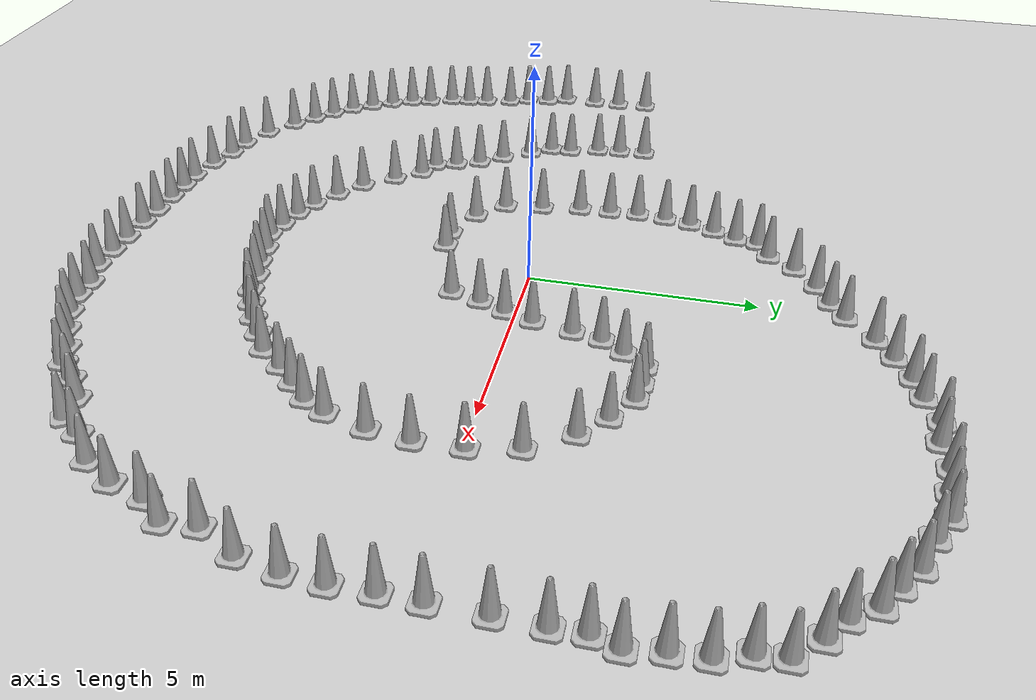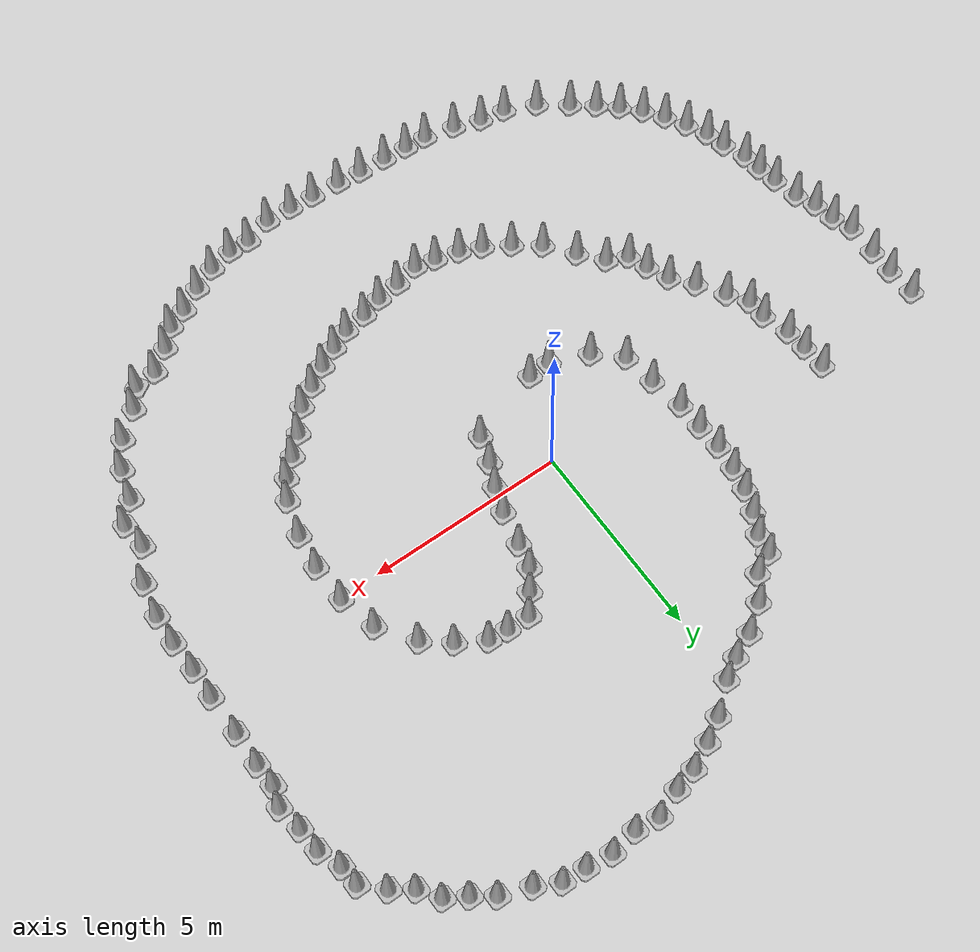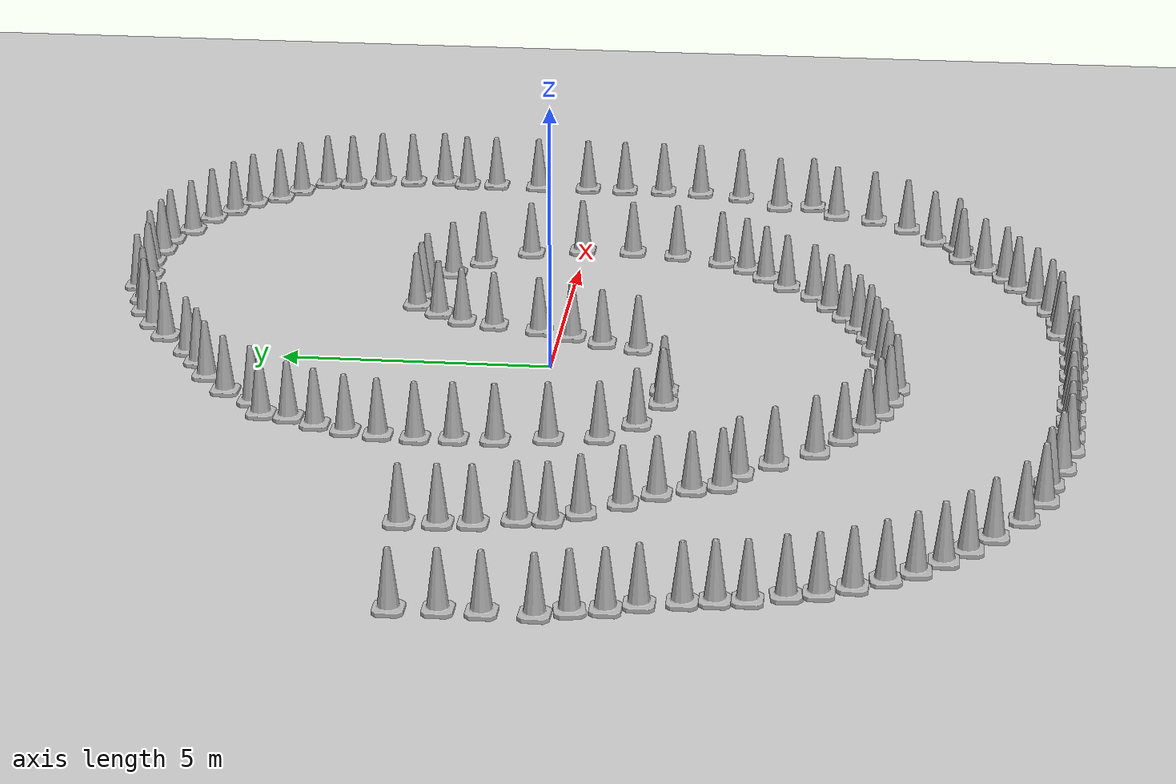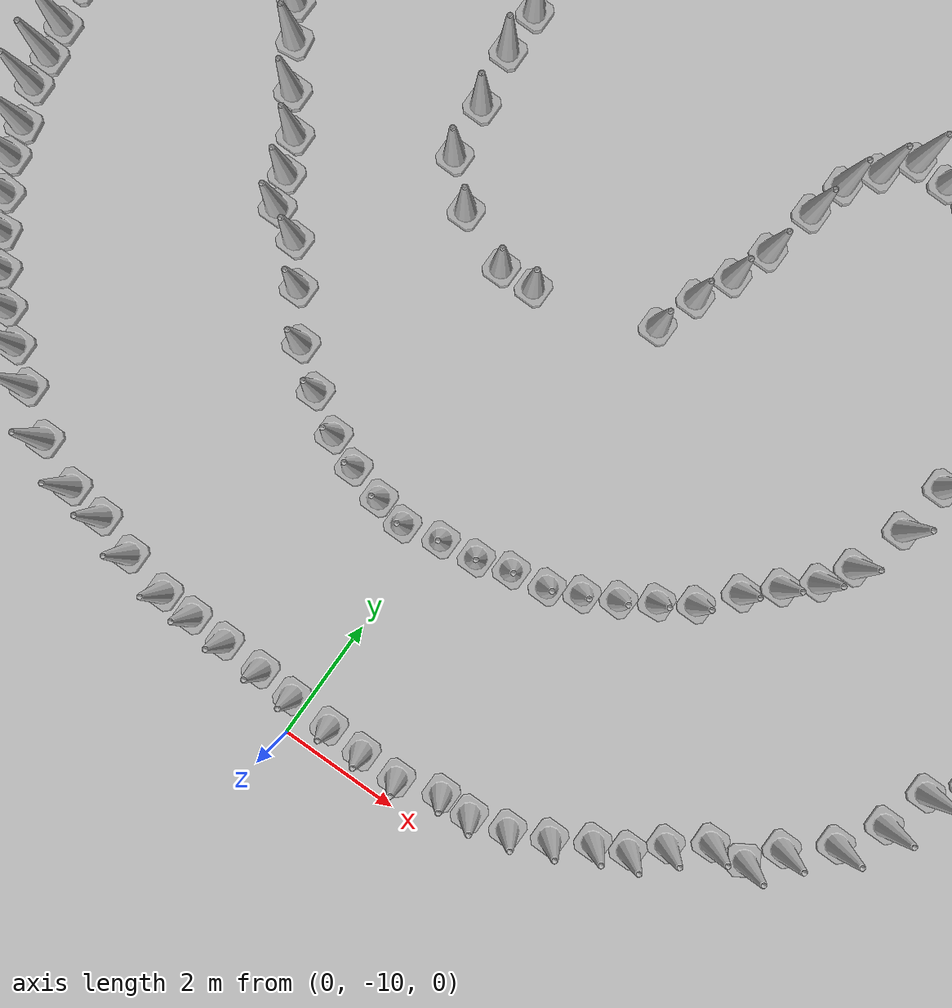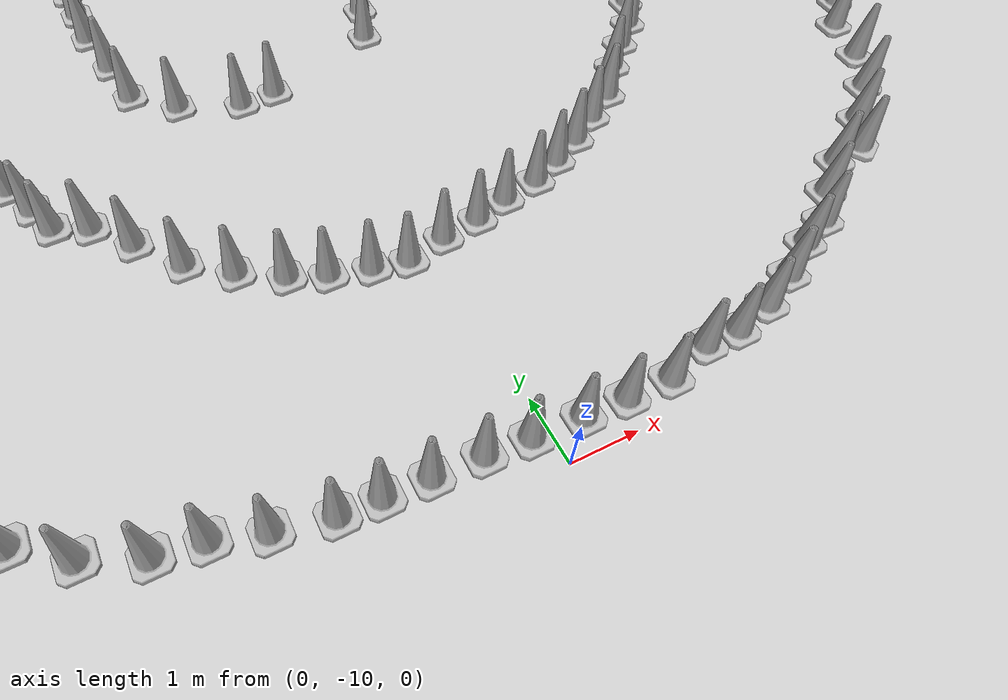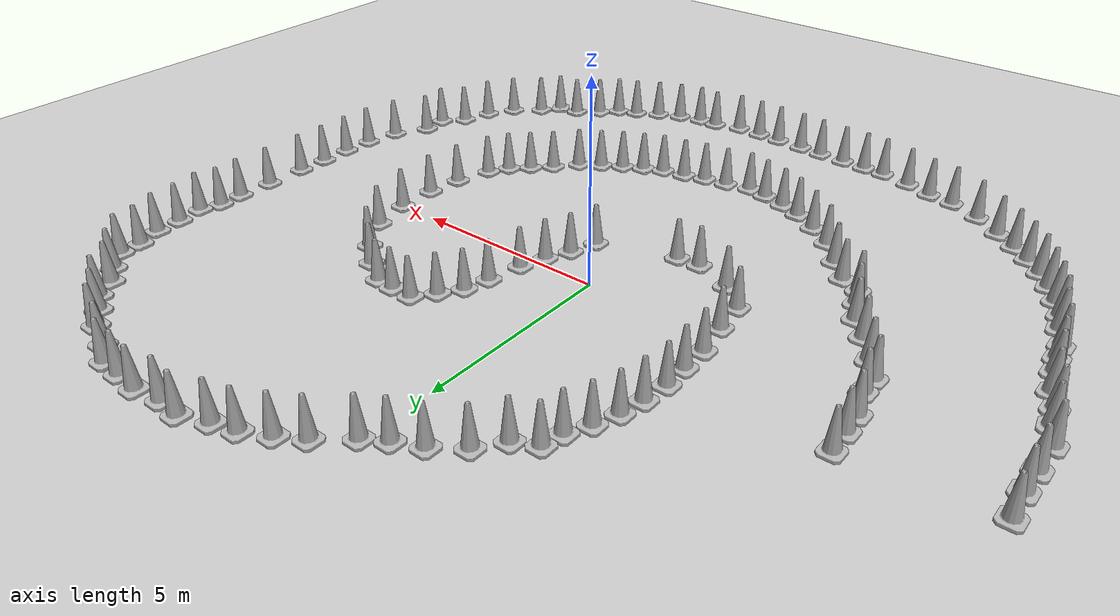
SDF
<sdf version="1.7">
 <world name="default">
  <light name="sun" type="directional">
   <pose>0 0 10 0 -0 0</pose>
   <diffuse>0.8 0.8 0.8 1</diffuse>
   <specular>0.2 0.2 0.2 1</specular>
   <attenuation>
    <range>1000</range>
    <constant>0.9</constant>
    <linear>0.01</linear>
    <quadratic>0.001</quadratic>
   </attenuation>
   <direction>-0.5 0.1 -0.9</direction>
   <spot><inner_angle>0</inner_angle><outer_angle>0</outer_angle><falloff>0</falloff></spot>
  </light>
  <model name="ground_plane">
   <static>1</static>
   <link name="link">
    <collision name="collision">
     <geometry><plane><normal>0 0 1</normal><size>100 100</size></plane></geometry>
     <surface>
      <contact><collide_bitmask>65535</collide_bitmask></contact>
      <friction><ode><mu>100</mu><mu2>50</mu2></ode></friction>
     </surface>
    </collision>
    <visual name="visual">
     <cast_shadows>0</cast_shadows>
     <geometry><plane><normal>0 0 1</normal><size>100 100</size></plane></geometry>
     <material>
      <script><uri>file://media/materials/scripts/gazebo.material</uri><name>Gazebo/Grey</name></script>
     </material>
    </visual>
   </link>
  </model>
  <gravity>0 0 -9.8</gravity>
  <magnetic_field>6e-06 2.3e-05 -4.2e-05</magnetic_field>
  <atmosphere type="adiabatic"/>
  <physics type="ode">
   <max_step_size>0.001</max_step_size>
   <real_time_factor>1</real_time_factor>
   <real_time_update_rate>1000</real_time_update_rate>
  </physics>
  <scene><ambient>0.4 0.4 0.4 1</ambient><background>0.7 0.7 0.7 1</background><shadows>1</shadows></scene>
  <audio><device>default</device></audio>
  <spherical_coordinates>
   <surface_model>EARTH_WGS84</surface_model>
   <latitude_deg>0</latitude_deg>
   <longitude_deg>0</longitude_deg>
   <elevation>0</elevation>
   <heading_deg>0</heading_deg>
  </spherical_coordinates>
  <model name="Construction Cone">
   <link name="link">
    <collision name="collision">
     <geometry>
      <mesh><scale>10 10 10</scale><uri>model://construction_cone/meshes/construction_cone.dae</uri></mesh>
     </geometry>
    </collision>
    <visual name="visual">
     <geometry>
      <mesh><scale>10 10 10</scale><uri>model://construction_cone/meshes/construction_cone.dae</uri></mesh>
     </geometry>
    </visual>
    <inertial>
     <inertia><ixx>1</ixx><ixy>0</ixy><ixz>0</ixz><iyy>1</iyy><iyz>0</iyz><izz>1</izz></inertia>
     <mass>1</mass>
    </inertial>
   </link>
   <pose>-3.44068 1.98693 -0 0 -0 0</pose>
  </model>
  <model name="Construction Cone_0">
   <link name="link">
    <collision name="collision">
     <geometry>
      <mesh><scale>10 10 10</scale><uri>model://construction_cone/meshes/construction_cone.dae</uri></mesh>
     </geometry>
    </collision>
    <visual name="visual">
     <geometry>
      <mesh><scale>10 10 10</scale><uri>model://construction_cone/meshes/construction_cone.dae</uri></mesh>
     </geometry>
    </visual>
    <inertial>
     <inertia><ixx>1</ixx><ixy>0</ixy><ixz>0</ixz><iyy>1</iyy><iyz>0</iyz><izz>1</izz></inertia>
     <mass>1</mass>
    </inertial>
   </link>
   <pose>-3.40166 1.31353 -0 0 -0 0</pose>
  </model>
  <model name="Construction Cone_1">
   <link name="link">
    <collision name="collision">
     <geometry>
      <mesh><scale>10 10 10</scale><uri>model://construction_cone/meshes/construction_cone.dae</uri></mesh>
     </geometry>
    </collision>
    <visual name="visual">
     <geometry>
      <mesh><scale>10 10 10</scale><uri>model://construction_cone/meshes/construction_cone.dae</uri></mesh>
     </geometry>
    </visual>
    <inertial>
     <inertia><ixx>1</ixx><ixy>0</ixy><ixz>0</ixz><iyy>1</iyy><iyz>0</iyz><izz>1</izz></inertia>
     <mass>1</mass>
    </inertial>
   </link>
   <pose>-3.38609 0.586652 -0 0 -1e-06 0</pose>
  </model>
  <model name="Construction Cone_2">
   <link name="link">
    <collision name="collision">
     <geometry>
      <mesh><scale>10 10 10</scale><uri>model://construction_cone/meshes/construction_cone.dae</uri></mesh>
     </geometry>
    </collision>
    <visual name="visual">
     <geometry>
      <mesh><scale>10 10 10</scale><uri>model://construction_cone/meshes/construction_cone.dae</uri></mesh>
     </geometry>
    </visual>
    <inertial>
     <inertia><ixx>1</ixx><ixy>0</ixy><ixz>0</ixz><iyy>1</iyy><iyz>0</iyz><izz>1</izz></inertia>
     <mass>1</mass>
    </inertial>
   </link>
   <pose>-3.23094 -0.328512 -0 0 -0 0</pose>
  </model>
  <model name="Construction Cone_3">
   <link name="link">
    <collision name="collision">
     <geometry>
      <mesh><scale>10 10 10</scale><uri>model://construction_cone/meshes/construction_cone.dae</uri></mesh>
     </geometry>
    </collision>
    <visual name="visual">
     <geometry>
      <mesh><scale>10 10 10</scale><uri>model://construction_cone/meshes/construction_cone.dae</uri></mesh>
     </geometry>
    </visual>
    <inertial>
     <inertia><ixx>1</ixx><ixy>0</ixy><ixz>0</ixz><iyy>1</iyy><iyz>0</iyz><izz>1</izz></inertia>
     <mass>1</mass>
    </inertial>
   </link>
   <pose>-3.10854 -1.21448 -0 0 -1e-06 0</pose>
  </model>
  <model name="Construction Cone_4">
   <link name="link">
    <collision name="collision">
     <geometry>
      <mesh><scale>10 10 10</scale><uri>model://construction_cone/meshes/construction_cone.dae</uri></mesh>
     </geometry>
    </collision>
    <visual name="visual">
     <geometry>
      <mesh><scale>10 10 10</scale><uri>model://construction_cone/meshes/construction_cone.dae</uri></mesh>
     </geometry>
    </visual>
    <inertial>
     <inertia><ixx>1</ixx><ixy>0</ixy><ixz>0</ixz><iyy>1</iyy><iyz>0</iyz><izz>1</izz></inertia>
     <mass>1</mass>
    </inertial>
   </link>
   <pose>-2.46633 -1.80717 -0 0 -1e-06 0</pose>
  </model>
  <model name="Construction Cone_5">
   <link name="link">
    <collision name="collision">
     <geometry>
      <mesh><scale>10 10 10</scale><uri>model://construction_cone/meshes/construction_cone.dae</uri></mesh>
     </geometry>
    </collision>
    <visual name="visual">
     <geometry>
      <mesh><scale>10 10 10</scale><uri>model://construction_cone/meshes/construction_cone.dae</uri></mesh>
     </geometry>
    </visual>
    <inertial>
     <inertia><ixx>1</ixx><ixy>0</ixy><ixz>0</ixz><iyy>1</iyy><iyz>0</iyz><izz>1</izz></inertia>
     <mass>1</mass>
    </inertial>
   </link>
   <pose>-1.51013 -2.19989 -0 0 -0 0</pose>
  </model>
  <model name="Construction Cone_6">
   <link name="link">
    <collision name="collision">
     <geometry>
      <mesh><scale>10 10 10</scale><uri>model://construction_cone/meshes/construction_cone.dae</uri></mesh>
     </geometry>
    </collision>
    <visual name="visual">
     <geometry>
      <mesh><scale>10 10 10</scale><uri>model://construction_cone/meshes/construction_cone.dae</uri></mesh>
     </geometry>
    </visual>
    <inertial>
     <inertia><ixx>1</ixx><ixy>0</ixy><ixz>0</ixz><iyy>1</iyy><iyz>0</iyz><izz>1</izz></inertia>
     <mass>1</mass>
    </inertial>
   </link>
   <pose>-0.921866 -2.16276 -0 0 -0 0</pose>
  </model>
  <model name="Construction Cone_7">
   <link name="link">
    <collision name="collision">
     <geometry>
      <mesh><scale>10 10 10</scale><uri>model://construction_cone/meshes/construction_cone.dae</uri></mesh>
     </geometry>
    </collision>
    <visual name="visual">
     <geometry>
      <mesh><scale>10 10 10</scale><uri>model://construction_cone/meshes/construction_cone.dae</uri></mesh>
     </geometry>
    </visual>
    <inertial>
     <inertia><ixx>1</ixx><ixy>0</ixy><ixz>0</ixz><iyy>1</iyy><iyz>0</iyz><izz>1</izz></inertia>
     <mass>1</mass>
    </inertial>
   </link>
   <pose>0.9944 -1.52269 -0 0 -1e-06 0</pose>
  </model>
  <model name="Construction Cone_8">
   <link name="link">
    <collision name="collision">
     <geometry>
      <mesh><scale>10 10 10</scale><uri>model://construction_cone/meshes/construction_cone.dae</uri></mesh>
     </geometry>
    </collision>
    <visual name="visual">
     <geometry>
      <mesh><scale>10 10 10</scale><uri>model://construction_cone/meshes/construction_cone.dae</uri></mesh>
     </geometry>
    </visual>
    <inertial>
     <inertia><ixx>1</ixx><ixy>0</ixy><ixz>0</ixz><iyy>1</iyy><iyz>0</iyz><izz>1</izz></inertia>
     <mass>1</mass>
    </inertial>
   </link>
   <pose>1.21662 -0.826146 -1e-05 -1e-06 0 0</pose>
  </model>
  <model name="Construction Cone_9">
   <link name="link">
    <collision name="collision">
     <geometry>
      <mesh><scale>10 10 10</scale><uri>model://construction_cone/meshes/construction_cone.dae</uri></mesh>
     </geometry>
    </collision>
    <visual name="visual">
     <geometry>
      <mesh><scale>10 10 10</scale><uri>model://construction_cone/meshes/construction_cone.dae</uri></mesh>
     </geometry>
    </visual>
    <inertial>
     <inertia><ixx>1</ixx><ixy>0</ixy><ixz>0</ixz><iyy>1</iyy><iyz>0</iyz><izz>1</izz></inertia>
     <mass>1</mass>
    </inertial>
   </link>
   <pose>1.71298 0.417313 -0 0 -0 0</pose>
  </model>
  <model name="Construction Cone_10">
   <link name="link">
    <collision name="collision">
     <geometry>
      <mesh><scale>10 10 10</scale><uri>model://construction_cone/meshes/construction_cone.dae</uri></mesh>
     </geometry>
    </collision>
    <visual name="visual">
     <geometry>
      <mesh><scale>10 10 10</scale><uri>model://construction_cone/meshes/construction_cone.dae</uri></mesh>
     </geometry>
    </visual>
    <inertial>
     <inertia><ixx>1</ixx><ixy>0</ixy><ixz>0</ixz><iyy>1</iyy><iyz>0</iyz><izz>1</izz></inertia>
     <mass>1</mass>
    </inertial>
   </link>
   <pose>2.05152 1.93247 -9e-06 -4e-06 1e-06 0.011427</pose>
  </model>
  <model name="Construction Cone_11">
   <link name="link">
    <collision name="collision">
     <geometry>
      <mesh><scale>10 10 10</scale><uri>model://construction_cone/meshes/construction_cone.dae</uri></mesh>
     </geometry>
    </collision>
    <visual name="visual">
     <geometry>
      <mesh><scale>10 10 10</scale><uri>model://construction_cone/meshes/construction_cone.dae</uri></mesh>
     </geometry>
    </visual>
    <inertial>
     <inertia><ixx>1</ixx><ixy>0</ixy><ixz>0</ixz><iyy>1</iyy><iyz>0</iyz><izz>1</izz></inertia>
     <mass>1</mass>
    </inertial>
   </link>
   <pose>3.85403 2.85734 -0 0 -0 0.002075</pose>
  </model>
  <model name="Construction Cone_12">
   <link name="link">
    <collision name="collision">
     <geometry>
      <mesh><scale>10 10 10</scale><uri>model://construction_cone/meshes/construction_cone.dae</uri></mesh>
     </geometry>
    </collision>
    <visual name="visual">
     <geometry>
      <mesh><scale>10 10 10</scale><uri>model://construction_cone/meshes/construction_cone.dae</uri></mesh>
     </geometry>
    </visual>
    <inertial>
     <inertia><ixx>1</ixx><ixy>0</ixy><ixz>0</ixz><iyy>1</iyy><iyz>0</iyz><izz>1</izz></inertia>
     <mass>1</mass>
    </inertial>
   </link>
   <pose>5.16762 1.9441 -0 0 -0 0</pose>
  </model>
  <model name="Construction Cone_13">
   <link name="link">
    <collision name="collision">
     <geometry>
      <mesh><scale>10 10 10</scale><uri>model://construction_cone/meshes/construction_cone.dae</uri></mesh>
     </geometry>
    </collision>
    <visual name="visual">
     <geometry>
      <mesh><scale>10 10 10</scale><uri>model://construction_cone/meshes/construction_cone.dae</uri></mesh>
     </geometry>
    </visual>
    <inertial>
     <inertia><ixx>1</ixx><ixy>0</ixy><ixz>0</ixz><iyy>1</iyy><iyz>0</iyz><izz>1</izz></inertia>
     <mass>1</mass>
    </inertial>
   </link>
   <pose>4.53615 2.45423 -0 0 -0 0</pose>
  </model>
  <model name="Construction Cone_14">
   <link name="link">
    <collision name="collision">
     <geometry>
      <mesh><scale>10 10 10</scale><uri>model://construction_cone/meshes/construction_cone.dae</uri></mesh>
     </geometry>
    </collision>
    <visual name="visual">
     <geometry>
      <mesh><scale>10 10 10</scale><uri>model://construction_cone/meshes/construction_cone.dae</uri></mesh>
     </geometry>
    </visual>
    <inertial>
     <inertia><ixx>1</ixx><ixy>0</ixy><ixz>0</ixz><iyy>1</iyy><iyz>0</iyz><izz>1</izz></inertia>
     <mass>1</mass>
    </inertial>
   </link>
   <pose>2.7693 2.90572 -0 0 -1e-06 -0.0056</pose>
  </model>
  <model name="Construction Cone_15">
   <link name="link">
    <collision name="collision">
     <geometry>
      <mesh><scale>10 10 10</scale><uri>model://construction_cone/meshes/construction_cone.dae</uri></mesh>
     </geometry>
    </collision>
    <visual name="visual">
     <geometry>
      <mesh><scale>10 10 10</scale><uri>model://construction_cone/meshes/construction_cone.dae</uri></mesh>
     </geometry>
    </visual>
    <inertial>
     <inertia><ixx>1</ixx><ixy>0</ixy><ixz>0</ixz><iyy>1</iyy><iyz>0</iyz><izz>1</izz></inertia>
     <mass>1</mass>
    </inertial>
   </link>
   <pose>1.49319 -0.228147 -0 0 -0 0</pose>
  </model>
  <model name="Construction Cone_16">
   <link name="link">
    <collision name="collision">
     <geometry>
      <mesh><scale>10 10 10</scale><uri>model://construction_cone/meshes/construction_cone.dae</uri></mesh>
     </geometry>
    </collision>
    <visual name="visual">
     <geometry>
      <mesh><scale>10 10 10</scale><uri>model://construction_cone/meshes/construction_cone.dae</uri></mesh>
     </geometry>
    </visual>
    <inertial>
     <inertia><ixx>1</ixx><ixy>0</ixy><ixz>0</ixz><iyy>1</iyy><iyz>0</iyz><izz>1</izz></inertia>
     <mass>1</mass>
    </inertial>
   </link>
   <pose>1.89693 1.29717 -0 0 -0 0</pose>
  </model>
  <model name="Construction Cone_17">
   <link name="link">
    <collision name="collision">
     <geometry>
      <mesh><scale>10 10 10</scale><uri>model://construction_cone/meshes/construction_cone.dae</uri></mesh>
     </geometry>
    </collision>
    <visual name="visual">
     <geometry>
      <mesh><scale>10 10 10</scale><uri>model://construction_cone/meshes/construction_cone.dae</uri></mesh>
     </geometry>
    </visual>
    <inertial>
     <inertia><ixx>1</ixx><ixy>0</ixy><ixz>0</ixz><iyy>1</iyy><iyz>0</iyz><izz>1</izz></inertia>
     <mass>1</mass>
    </inertial>
   </link>
   <pose>5.79564 1.05787 -0 0 -1e-06 0</pose>
  </model>
  <model name="Construction Cone_18">
   <link name="link">
    <collision name="collision">
     <geometry>
      <mesh><scale>10 10 10</scale><uri>model://construction_cone/meshes/construction_cone.dae</uri></mesh>
     </geometry>
    </collision>
    <visual name="visual">
     <geometry>
      <mesh><scale>10 10 10</scale><uri>model://construction_cone/meshes/construction_cone.dae</uri></mesh>
     </geometry>
    </visual>
    <inertial>
     <inertia><ixx>1</ixx><ixy>0</ixy><ixz>0</ixz><iyy>1</iyy><iyz>0</iyz><izz>1</izz></inertia>
     <mass>1</mass>
    </inertial>
   </link>
   <pose>6.02414 0.046803 -0 0 -0 0</pose>
  </model>
  <model name="Construction Cone_19">
   <link name="link">
    <collision name="collision">
     <geometry>
      <mesh><scale>10 10 10</scale><uri>model://construction_cone/meshes/construction_cone.dae</uri></mesh>
     </geometry>
    </collision>
    <visual name="visual">
     <geometry>
      <mesh><scale>10 10 10</scale><uri>model://construction_cone/meshes/construction_cone.dae</uri></mesh>
     </geometry>
    </visual>
    <inertial>
     <inertia><ixx>1</ixx><ixy>0</ixy><ixz>0</ixz><iyy>1</iyy><iyz>0</iyz><izz>1</izz></inertia>
     <mass>1</mass>
    </inertial>
   </link>
   <pose>6.05028 -0.964695 -0 0 -0 0</pose>
  </model>
  <model name="Construction Cone_20">
   <link name="link">
    <collision name="collision">
     <geometry>
      <mesh><scale>10 10 10</scale><uri>model://construction_cone/meshes/construction_cone.dae</uri></mesh>
     </geometry>
    </collision>
    <visual name="visual">
     <geometry>
      <mesh><scale>10 10 10</scale><uri>model://construction_cone/meshes/construction_cone.dae</uri></mesh>
     </geometry>
    </visual>
    <inertial>
     <inertia><ixx>1</ixx><ixy>0</ixy><ixz>0</ixz><iyy>1</iyy><iyz>0</iyz><izz>1</izz></inertia>
     <mass>1</mass>
    </inertial>
   </link>
   <pose>5.92745 -1.8709 -0 -0 -0 -0</pose>
  </model>
  <model name="Construction Cone_21">
   <link name="link">
    <collision name="collision">
     <geometry>
      <mesh><scale>10 10 10</scale><uri>model://construction_cone/meshes/construction_cone.dae</uri></mesh>
     </geometry>
    </collision>
    <visual name="visual">
     <geometry>
      <mesh><scale>10 10 10</scale><uri>model://construction_cone/meshes/construction_cone.dae</uri></mesh>
     </geometry>
    </visual>
    <inertial>
     <inertia><ixx>1</ixx><ixy>0</ixy><ixz>0</ixz><iyy>1</iyy><iyz>0</iyz><izz>1</izz></inertia>
     <mass>1</mass>
    </inertial>
   </link>
   <pose>5.64955 -2.78002 -0 0 -1e-06 0</pose>
  </model>
  <model name="Construction Cone_22">
   <link name="link">
    <collision name="collision">
     <geometry>
      <mesh><scale>10 10 10</scale><uri>model://construction_cone/meshes/construction_cone.dae</uri></mesh>
     </geometry>
    </collision>
    <visual name="visual">
     <geometry>
      <mesh><scale>10 10 10</scale><uri>model://construction_cone/meshes/construction_cone.dae</uri></mesh>
     </geometry>
    </visual>
    <inertial>
     <inertia><ixx>1</ixx><ixy>0</ixy><ixz>0</ixz><iyy>1</iyy><iyz>0</iyz><izz>1</izz></inertia>
     <mass>1</mass>
    </inertial>
   </link>
   <pose>0.05073 6.79197 -0 0 -0 0.001801</pose>
  </model>
  <model name="Construction Cone_23">
   <link name="link">
    <collision name="collision">
     <geometry>
      <mesh><scale>10 10 10</scale><uri>model://construction_cone/meshes/construction_cone.dae</uri></mesh>
     </geometry>
    </collision>
    <visual name="visual">
     <geometry>
      <mesh><scale>10 10 10</scale><uri>model://construction_cone/meshes/construction_cone.dae</uri></mesh>
     </geometry>
    </visual>
    <inertial>
     <inertia><ixx>1</ixx><ixy>0</ixy><ixz>0</ixz><iyy>1</iyy><iyz>0</iyz><izz>1</izz></inertia>
     <mass>1</mass>
    </inertial>
   </link>
   <pose>1.3178 7.72218 -1e-05 -1e-06 0 0</pose>
  </model>
  <model name="Construction Cone_24">
   <link name="link">
    <collision name="collision">
     <geometry>
      <mesh><scale>10 10 10</scale><uri>model://construction_cone/meshes/construction_cone.dae</uri></mesh>
     </geometry>
    </collision>
    <visual name="visual">
     <geometry>
      <mesh><scale>10 10 10</scale><uri>model://construction_cone/meshes/construction_cone.dae</uri></mesh>
     </geometry>
    </visual>
    <inertial>
     <inertia><ixx>1</ixx><ixy>0</ixy><ixz>0</ixz><iyy>1</iyy><iyz>0</iyz><izz>1</izz></inertia>
     <mass>1</mass>
    </inertial>
   </link>
   <pose>0.746636 7.3753 -0 0 -0 0</pose>
  </model>
  <model name="Construction Cone_25">
   <link name="link">
    <collision name="collision">
     <geometry>
      <mesh><scale>10 10 10</scale><uri>model://construction_cone/meshes/construction_cone.dae</uri></mesh>
     </geometry>
    </collision>
    <visual name="visual">
     <geometry>
      <mesh><scale>10 10 10</scale><uri>model://construction_cone/meshes/construction_cone.dae</uri></mesh>
     </geometry>
    </visual>
    <inertial>
     <inertia><ixx>1</ixx><ixy>0</ixy><ixz>0</ixz><iyy>1</iyy><iyz>0</iyz><izz>1</izz></inertia>
     <mass>1</mass>
    </inertial>
   </link>
   <pose>2.54045 8.20519 -0 0 -0 0</pose>
  </model>
  <model name="Construction Cone_26">
   <link name="link">
    <collision name="collision">
     <geometry>
      <mesh><scale>10 10 10</scale><uri>model://construction_cone/meshes/construction_cone.dae</uri></mesh>
     </geometry>
    </collision>
    <visual name="visual">
     <geometry>
      <mesh><scale>10 10 10</scale><uri>model://construction_cone/meshes/construction_cone.dae</uri></mesh>
     </geometry>
    </visual>
    <inertial>
     <inertia><ixx>1</ixx><ixy>0</ixy><ixz>0</ixz><iyy>1</iyy><iyz>0</iyz><izz>1</izz></inertia>
     <mass>1</mass>
    </inertial>
   </link>
   <pose>3.85646 8.41084 -1e-05 -1e-06 0 0</pose>
  </model>
  <model name="Construction Cone_27">
   <link name="link">
    <collision name="collision">
     <geometry>
      <mesh><scale>10 10 10</scale><uri>model://construction_cone/meshes/construction_cone.dae</uri></mesh>
     </geometry>
    </collision>
    <visual name="visual">
     <geometry>
      <mesh><scale>10 10 10</scale><uri>model://construction_cone/meshes/construction_cone.dae</uri></mesh>
     </geometry>
    </visual>
    <inertial>
     <inertia><ixx>1</ixx><ixy>0</ixy><ixz>0</ixz><iyy>1</iyy><iyz>0</iyz><izz>1</izz></inertia>
     <mass>1</mass>
    </inertial>
   </link>
   <pose>5.23108 8.46225 -0 0 -0 0</pose>
  </model>
  <model name="Construction Cone_28">
   <link name="link">
    <collision name="collision">
     <geometry>
      <mesh><scale>10 10 10</scale><uri>model://construction_cone/meshes/construction_cone.dae</uri></mesh>
     </geometry>
    </collision>
    <visual name="visual">
     <geometry>
      <mesh><scale>10 10 10</scale><uri>model://construction_cone/meshes/construction_cone.dae</uri></mesh>
     </geometry>
    </visual>
    <inertial>
     <inertia><ixx>1</ixx><ixy>0</ixy><ixz>0</ixz><iyy>1</iyy><iyz>0</iyz><izz>1</izz></inertia>
     <mass>1</mass>
    </inertial>
   </link>
   <pose>6.41788 8.11984 -0 0 -0 0</pose>
  </model>
  <model name="Construction Cone_29">
   <link name="link">
    <collision name="collision">
     <geometry>
      <mesh><scale>10 10 10</scale><uri>model://construction_cone/meshes/construction_cone.dae</uri></mesh>
     </geometry>
    </collision>
    <visual name="visual">
     <geometry>
      <mesh><scale>10 10 10</scale><uri>model://construction_cone/meshes/construction_cone.dae</uri></mesh>
     </geometry>
    </visual>
    <inertial>
     <inertia><ixx>1</ixx><ixy>0</ixy><ixz>0</ixz><iyy>1</iyy><iyz>0</iyz><izz>1</izz></inertia>
     <mass>1</mass>
    </inertial>
   </link>
   <pose>7.65812 7.49906 0 -1e-06 0 0.004828</pose>
  </model>
  <model name="Construction Cone_30">
   <link name="link">
    <collision name="collision">
     <geometry>
      <mesh><scale>10 10 10</scale><uri>model://construction_cone/meshes/construction_cone.dae</uri></mesh>
     </geometry>
    </collision>
    <visual name="visual">
     <geometry>
      <mesh><scale>10 10 10</scale><uri>model://construction_cone/meshes/construction_cone.dae</uri></mesh>
     </geometry>
    </visual>
    <inertial>
     <inertia><ixx>1</ixx><ixy>0</ixy><ixz>0</ixz><iyy>1</iyy><iyz>0</iyz><izz>1</izz></inertia>
     <mass>1</mass>
    </inertial>
   </link>
   <pose>8.51314 6.69867 -0 0 0 -0.005858</pose>
  </model>
  <model name="Construction Cone_31">
   <link name="link">
    <collision name="collision">
     <geometry>
      <mesh><scale>10 10 10</scale><uri>model://construction_cone/meshes/construction_cone.dae</uri></mesh>
     </geometry>
    </collision>
    <visual name="visual">
     <geometry>
      <mesh><scale>10 10 10</scale><uri>model://construction_cone/meshes/construction_cone.dae</uri></mesh>
     </geometry>
    </visual>
    <inertial>
     <inertia><ixx>1</ixx><ixy>0</ixy><ixz>0</ixz><iyy>1</iyy><iyz>0</iyz><izz>1</izz></inertia>
     <mass>1</mass>
    </inertial>
   </link>
   <pose>9.50204 5.86042 -0 0 -1e-06 0</pose>
  </model>
  <model name="Construction Cone_32">
   <link name="link">
    <collision name="collision">
     <geometry>
      <mesh><scale>10 10 10</scale><uri>model://construction_cone/meshes/construction_cone.dae</uri></mesh>
     </geometry>
    </collision>
    <visual name="visual">
     <geometry>
      <mesh><scale>10 10 10</scale><uri>model://construction_cone/meshes/construction_cone.dae</uri></mesh>
     </geometry>
    </visual>
    <inertial>
     <inertia><ixx>1</ixx><ixy>0</ixy><ixz>0</ixz><iyy>1</iyy><iyz>0</iyz><izz>1</izz></inertia>
     <mass>1</mass>
    </inertial>
   </link>
   <pose>9.76937 4.72472 -1e-05 0 -0 0</pose>
  </model>
  <model name="Construction Cone_33">
   <link name="link">
    <collision name="collision">
     <geometry>
      <mesh><scale>10 10 10</scale><uri>model://construction_cone/meshes/construction_cone.dae</uri></mesh>
     </geometry>
    </collision>
    <visual name="visual">
     <geometry>
      <mesh><scale>10 10 10</scale><uri>model://construction_cone/meshes/construction_cone.dae</uri></mesh>
     </geometry>
    </visual>
    <inertial>
     <inertia><ixx>1</ixx><ixy>0</ixy><ixz>0</ixz><iyy>1</iyy><iyz>0</iyz><izz>1</izz></inertia>
     <mass>1</mass>
    </inertial>
   </link>
   <pose>9.91562 3.41143 -0 0 -1e-06 0.002152</pose>
  </model>
  <model name="Construction Cone_34">
   <link name="link">
    <collision name="collision">
     <geometry>
      <mesh><scale>10 10 10</scale><uri>model://construction_cone/meshes/construction_cone.dae</uri></mesh>
     </geometry>
    </collision>
    <visual name="visual">
     <geometry>
      <mesh><scale>10 10 10</scale><uri>model://construction_cone/meshes/construction_cone.dae</uri></mesh>
     </geometry>
    </visual>
    <inertial>
     <inertia><ixx>1</ixx><ixy>0</ixy><ixz>0</ixz><iyy>1</iyy><iyz>0</iyz><izz>1</izz></inertia>
     <mass>1</mass>
    </inertial>
   </link>
   <pose>9.77014 2.28502 0 -0 -0 -0</pose>
  </model>
  <model name="Construction Cone_35">
   <link name="link">
    <collision name="collision">
     <geometry>
      <mesh><scale>10 10 10</scale><uri>model://construction_cone/meshes/construction_cone.dae</uri></mesh>
     </geometry>
    </collision>
    <visual name="visual">
     <geometry>
      <mesh><scale>10 10 10</scale><uri>model://construction_cone/meshes/construction_cone.dae</uri></mesh>
     </geometry>
    </visual>
    <inertial>
     <inertia><ixx>1</ixx><ixy>0</ixy><ixz>0</ixz><iyy>1</iyy><iyz>0</iyz><izz>1</izz></inertia>
     <mass>1</mass>
    </inertial>
   </link>
   <pose>9.74625 1.38212 -0 0 -0 0</pose>
  </model>
  <model name="Construction Cone_36">
   <link name="link">
    <collision name="collision">
     <geometry>
      <mesh><scale>10 10 10</scale><uri>model://construction_cone/meshes/construction_cone.dae</uri></mesh>
     </geometry>
    </collision>
    <visual name="visual">
     <geometry>
      <mesh><scale>10 10 10</scale><uri>model://construction_cone/meshes/construction_cone.dae</uri></mesh>
     </geometry>
    </visual>
    <inertial>
     <inertia><ixx>1</ixx><ixy>0</ixy><ixz>0</ixz><iyy>1</iyy><iyz>0</iyz><izz>1</izz></inertia>
     <mass>1</mass>
    </inertial>
   </link>
   <pose>9.73989 0.328505 -0 0 -1e-06 0</pose>
  </model>
  <model name="Construction Cone_37">
   <link name="link">
    <collision name="collision">
     <geometry>
      <mesh><scale>10 10 10</scale><uri>model://construction_cone/meshes/construction_cone.dae</uri></mesh>
     </geometry>
    </collision>
    <visual name="visual">
     <geometry>
      <mesh><scale>10 10 10</scale><uri>model://construction_cone/meshes/construction_cone.dae</uri></mesh>
     </geometry>
    </visual>
    <inertial>
     <inertia><ixx>1</ixx><ixy>0</ixy><ixz>0</ixz><iyy>1</iyy><iyz>0</iyz><izz>1</izz></inertia>
     <mass>1</mass>
    </inertial>
   </link>
   <pose>9.71702 -0.459126 -0 0 -0 0</pose>
  </model>
  <model name="Construction Cone_38">
   <link name="link">
    <collision name="collision">
     <geometry>
      <mesh><scale>10 10 10</scale><uri>model://construction_cone/meshes/construction_cone.dae</uri></mesh>
     </geometry>
    </collision>
    <visual name="visual">
     <geometry>
      <mesh><scale>10 10 10</scale><uri>model://construction_cone/meshes/construction_cone.dae</uri></mesh>
     </geometry>
    </visual>
    <inertial>
     <inertia><ixx>1</ixx><ixy>0</ixy><ixz>0</ixz><iyy>1</iyy><iyz>0</iyz><izz>1</izz></inertia>
     <mass>1</mass>
    </inertial>
   </link>
   <pose>9.73359 -1.27782 -0 0 -1e-06 0</pose>
  </model>
  <model name="Construction Cone_39">
   <link name="link">
    <collision name="collision">
     <geometry>
      <mesh><scale>10 10 10</scale><uri>model://construction_cone/meshes/construction_cone.dae</uri></mesh>
     </geometry>
    </collision>
    <visual name="visual">
     <geometry>
      <mesh><scale>10 10 10</scale><uri>model://construction_cone/meshes/construction_cone.dae</uri></mesh>
     </geometry>
    </visual>
    <inertial>
     <inertia><ixx>1</ixx><ixy>0</ixy><ixz>0</ixz><iyy>1</iyy><iyz>0</iyz><izz>1</izz></inertia>
     <mass>1</mass>
    </inertial>
   </link>
   <pose>9.68814 -2.06783 -0 0 -0 0</pose>
  </model>
  <model name="Construction Cone_40">
   <link name="link">
    <collision name="collision">
     <geometry>
      <mesh><scale>10 10 10</scale><uri>model://construction_cone/meshes/construction_cone.dae</uri></mesh>
     </geometry>
    </collision>
    <visual name="visual">
     <geometry>
      <mesh><scale>10 10 10</scale><uri>model://construction_cone/meshes/construction_cone.dae</uri></mesh>
     </geometry>
    </visual>
    <inertial>
     <inertia><ixx>1</ixx><ixy>0</ixy><ixz>0</ixz><iyy>1</iyy><iyz>0</iyz><izz>1</izz></inertia>
     <mass>1</mass>
    </inertial>
   </link>
   <pose>9.50201 -2.93854 0 -0 -0 -0</pose>
  </model>
  <model name="Construction Cone_41">
   <link name="link">
    <collision name="collision">
     <geometry>
      <mesh><scale>10 10 10</scale><uri>model://construction_cone/meshes/construction_cone.dae</uri></mesh>
     </geometry>
    </collision>
    <visual name="visual">
     <geometry>
      <mesh><scale>10 10 10</scale><uri>model://construction_cone/meshes/construction_cone.dae</uri></mesh>
     </geometry>
    </visual>
    <inertial>
     <inertia><ixx>1</ixx><ixy>0</ixy><ixz>0</ixz><iyy>1</iyy><iyz>0</iyz><izz>1</izz></inertia>
     <mass>1</mass>
    </inertial>
   </link>
   <pose>9.02595 -3.76232 -0 0 -1e-06 0</pose>
  </model>
  <model name="Construction Cone_42">
   <link name="link">
    <collision name="collision">
     <geometry>
      <mesh><scale>10 10 10</scale><uri>model://construction_cone/meshes/construction_cone.dae</uri></mesh>
     </geometry>
    </collision>
    <visual name="visual">
     <geometry>
      <mesh><scale>10 10 10</scale><uri>model://construction_cone/meshes/construction_cone.dae</uri></mesh>
     </geometry>
    </visual>
    <inertial>
     <inertia><ixx>1</ixx><ixy>0</ixy><ixz>0</ixz><iyy>1</iyy><iyz>0</iyz><izz>1</izz></inertia>
     <mass>1</mass>
    </inertial>
   </link>
   <pose>9.00707 6.34854 -0 0 -1e-06 0.003849</pose>
  </model>
  <model name="Construction Cone_43">
   <link name="link">
    <collision name="collision">
     <geometry>
      <mesh><scale>10 10 10</scale><uri>model://construction_cone/meshes/construction_cone.dae</uri></mesh>
     </geometry>
    </collision>
    <visual name="visual">
     <geometry>
      <mesh><scale>10 10 10</scale><uri>model://construction_cone/meshes/construction_cone.dae</uri></mesh>
     </geometry>
    </visual>
    <inertial>
     <inertia><ixx>1</ixx><ixy>0</ixy><ixz>0</ixz><iyy>1</iyy><iyz>0</iyz><izz>1</izz></inertia>
     <mass>1</mass>
    </inertial>
   </link>
   <pose>8.16303 7.19222 -0 0 -1e-06 0.006167</pose>
  </model>
  <model name="Construction Cone_44">
   <link name="link">
    <collision name="collision">
     <geometry>
      <mesh><scale>10 10 10</scale><uri>model://construction_cone/meshes/construction_cone.dae</uri></mesh>
     </geometry>
    </collision>
    <visual name="visual">
     <geometry>
      <mesh><scale>10 10 10</scale><uri>model://construction_cone/meshes/construction_cone.dae</uri></mesh>
     </geometry>
    </visual>
    <inertial>
     <inertia><ixx>1</ixx><ixy>0</ixy><ixz>0</ixz><iyy>1</iyy><iyz>0</iyz><izz>1</izz></inertia>
     <mass>1</mass>
    </inertial>
   </link>
   <pose>7.1635 7.8478 -0 0 0 -0.000834</pose>
  </model>
  <model name="Construction Cone_45">
   <link name="link">
    <collision name="collision">
     <geometry>
      <mesh><scale>10 10 10</scale><uri>model://construction_cone/meshes/construction_cone.dae</uri></mesh>
     </geometry>
    </collision>
    <visual name="visual">
     <geometry>
      <mesh><scale>10 10 10</scale><uri>model://construction_cone/meshes/construction_cone.dae</uri></mesh>
     </geometry>
    </visual>
    <inertial>
     <inertia><ixx>1</ixx><ixy>0</ixy><ixz>0</ixz><iyy>1</iyy><iyz>0</iyz><izz>1</izz></inertia>
     <mass>1</mass>
    </inertial>
   </link>
   <pose>5.84006 8.41833 -0 0 -1e-06 0</pose>
  </model>
  <model name="Construction Cone_46">
   <link name="link">
    <collision name="collision">
     <geometry>
      <mesh><scale>10 10 10</scale><uri>model://construction_cone/meshes/construction_cone.dae</uri></mesh>
     </geometry>
    </collision>
    <visual name="visual">
     <geometry>
      <mesh><scale>10 10 10</scale><uri>model://construction_cone/meshes/construction_cone.dae</uri></mesh>
     </geometry>
    </visual>
    <inertial>
     <inertia><ixx>1</ixx><ixy>0</ixy><ixz>0</ixz><iyy>1</iyy><iyz>0</iyz><izz>1</izz></inertia>
     <mass>1</mass>
    </inertial>
   </link>
   <pose>4.56602 8.53689 -0 0 -1e-06 0</pose>
  </model>
  <model name="Construction Cone_47">
   <link name="link">
    <collision name="collision">
     <geometry>
      <mesh><scale>10 10 10</scale><uri>model://construction_cone/meshes/construction_cone.dae</uri></mesh>
     </geometry>
    </collision>
    <visual name="visual">
     <geometry>
      <mesh><scale>10 10 10</scale><uri>model://construction_cone/meshes/construction_cone.dae</uri></mesh>
     </geometry>
    </visual>
    <inertial>
     <inertia><ixx>1</ixx><ixy>0</ixy><ixz>0</ixz><iyy>1</iyy><iyz>0</iyz><izz>1</izz></inertia>
     <mass>1</mass>
    </inertial>
   </link>
   <pose>3.23226 8.47665 -3e-06 -4e-06 -1e-06 0</pose>
  </model>
  <model name="Construction Cone_48">
   <link name="link">
    <collision name="collision">
     <geometry>
      <mesh><scale>10 10 10</scale><uri>model://construction_cone/meshes/construction_cone.dae</uri></mesh>
     </geometry>
    </collision>
    <visual name="visual">
     <geometry>
      <mesh><scale>10 10 10</scale><uri>model://construction_cone/meshes/construction_cone.dae</uri></mesh>
     </geometry>
    </visual>
    <inertial>
     <inertia><ixx>1</ixx><ixy>0</ixy><ixz>0</ixz><iyy>1</iyy><iyz>0</iyz><izz>1</izz></inertia>
     <mass>1</mass>
    </inertial>
   </link>
   <pose>1.9475 8.04268 -0 0 -0 0</pose>
  </model>
  <model name="Construction Cone_49">
   <link name="link">
    <collision name="collision">
     <geometry>
      <mesh><scale>10 10 10</scale><uri>model://construction_cone/meshes/construction_cone.dae</uri></mesh>
     </geometry>
    </collision>
    <visual name="visual">
     <geometry>
      <mesh><scale>10 10 10</scale><uri>model://construction_cone/meshes/construction_cone.dae</uri></mesh>
     </geometry>
    </visual>
    <inertial>
     <inertia><ixx>1</ixx><ixy>0</ixy><ixz>0</ixz><iyy>1</iyy><iyz>0</iyz><izz>1</izz></inertia>
     <mass>1</mass>
    </inertial>
   </link>
   <pose>-0.452202 6.48631 -0 0 0 -0.000383</pose>
  </model>
  <model name="Construction Cone_50">
   <link name="link">
    <collision name="collision">
     <geometry>
      <mesh><scale>10 10 10</scale><uri>model://construction_cone/meshes/construction_cone.dae</uri></mesh>
     </geometry>
    </collision>
    <visual name="visual">
     <geometry>
      <mesh><scale>10 10 10</scale><uri>model://construction_cone/meshes/construction_cone.dae</uri></mesh>
     </geometry>
    </visual>
    <inertial>
     <inertia><ixx>1</ixx><ixy>0</ixy><ixz>0</ixz><iyy>1</iyy><iyz>0</iyz><izz>1</izz></inertia>
     <mass>1</mass>
    </inertial>
   </link>
   <pose>-1.0673 6.19671 -0 0 -1e-06 0</pose>
  </model>
  <model name="Construction Cone_51">
   <link name="link">
    <collision name="collision">
     <geometry>
      <mesh><scale>10 10 10</scale><uri>model://construction_cone/meshes/construction_cone.dae</uri></mesh>
     </geometry>
    </collision>
    <visual name="visual">
     <geometry>
      <mesh><scale>10 10 10</scale><uri>model://construction_cone/meshes/construction_cone.dae</uri></mesh>
     </geometry>
    </visual>
    <inertial>
     <inertia><ixx>1</ixx><ixy>0</ixy><ixz>0</ixz><iyy>1</iyy><iyz>0</iyz><izz>1</izz></inertia>
     <mass>1</mass>
    </inertial>
   </link>
   <pose>-1.71318 5.71714 0 -0 -0 -0</pose>
  </model>
  <model name="Construction Cone_52">
   <link name="link">
    <collision name="collision">
     <geometry>
      <mesh><scale>10 10 10</scale><uri>model://construction_cone/meshes/construction_cone.dae</uri></mesh>
     </geometry>
    </collision>
    <visual name="visual">
     <geometry>
      <mesh><scale>10 10 10</scale><uri>model://construction_cone/meshes/construction_cone.dae</uri></mesh>
     </geometry>
    </visual>
    <inertial>
     <inertia><ixx>1</ixx><ixy>0</ixy><ixz>0</ixz><iyy>1</iyy><iyz>0</iyz><izz>1</izz></inertia>
     <mass>1</mass>
    </inertial>
   </link>
   <pose>-2.14539 5.13354 -0 0 -1e-06 0</pose>
  </model>
  <model name="Construction Cone_53">
   <link name="link">
    <collision name="collision">
     <geometry>
      <mesh><scale>10 10 10</scale><uri>model://construction_cone/meshes/construction_cone.dae</uri></mesh>
     </geometry>
    </collision>
    <visual name="visual">
     <geometry>
      <mesh><scale>10 10 10</scale><uri>model://construction_cone/meshes/construction_cone.dae</uri></mesh>
     </geometry>
    </visual>
    <inertial>
     <inertia><ixx>1</ixx><ixy>0</ixy><ixz>0</ixz><iyy>1</iyy><iyz>0</iyz><izz>1</izz></inertia>
     <mass>1</mass>
    </inertial>
   </link>
   <pose>-3.36483 2.65519 -0 0 -0 0</pose>
  </model>
  <model name="Construction Cone_54">
   <link name="link">
    <collision name="collision">
     <geometry>
      <mesh><scale>10 10 10</scale><uri>model://construction_cone/meshes/construction_cone.dae</uri></mesh>
     </geometry>
    </collision>
    <visual name="visual">
     <geometry>
      <mesh><scale>10 10 10</scale><uri>model://construction_cone/meshes/construction_cone.dae</uri></mesh>
     </geometry>
    </visual>
    <inertial>
     <inertia><ixx>1</ixx><ixy>0</ixy><ixz>0</ixz><iyy>1</iyy><iyz>0</iyz><izz>1</izz></inertia>
     <mass>1</mass>
    </inertial>
   </link>
   <pose>-3.2459 3.25522 -0 0 -0 0</pose>
  </model>
  <model name="Construction Cone_55">
   <link name="link">
    <collision name="collision">
     <geometry>
      <mesh><scale>10 10 10</scale><uri>model://construction_cone/meshes/construction_cone.dae</uri></mesh>
     </geometry>
    </collision>
    <visual name="visual">
     <geometry>
      <mesh><scale>10 10 10</scale><uri>model://construction_cone/meshes/construction_cone.dae</uri></mesh>
     </geometry>
    </visual>
    <inertial>
     <inertia><ixx>1</ixx><ixy>0</ixy><ixz>0</ixz><iyy>1</iyy><iyz>0</iyz><izz>1</izz></inertia>
     <mass>1</mass>
    </inertial>
   </link>
   <pose>-3.03473 3.83269 -0 0 -0 0</pose>
  </model>
  <model name="Construction Cone_56">
   <link name="link">
    <collision name="collision">
     <geometry>
      <mesh><scale>10 10 10</scale><uri>model://construction_cone/meshes/construction_cone.dae</uri></mesh>
     </geometry>
    </collision>
    <visual name="visual">
     <geometry>
      <mesh><scale>10 10 10</scale><uri>model://construction_cone/meshes/construction_cone.dae</uri></mesh>
     </geometry>
    </visual>
    <inertial>
     <inertia><ixx>1</ixx><ixy>0</ixy><ixz>0</ixz><iyy>1</iyy><iyz>0</iyz><izz>1</izz></inertia>
     <mass>1</mass>
    </inertial>
   </link>
   <pose>-2.76935 4.35747 -0 0 -1e-06 0</pose>
  </model>
  <model name="Construction Cone_57">
   <link name="link">
    <collision name="collision">
     <geometry>
      <mesh><scale>10 10 10</scale><uri>model://construction_cone/meshes/construction_cone.dae</uri></mesh>
     </geometry>
    </collision>
    <visual name="visual">
     <geometry>
      <mesh><scale>10 10 10</scale><uri>model://construction_cone/meshes/construction_cone.dae</uri></mesh>
     </geometry>
    </visual>
    <inertial>
     <inertia><ixx>1</ixx><ixy>0</ixy><ixz>0</ixz><iyy>1</iyy><iyz>0</iyz><izz>1</izz></inertia>
     <mass>1</mass>
    </inertial>
   </link>
   <pose>-2.66975 4.8703 -0 0 -0 0</pose>
  </model>
  <model name="Construction Cone_58">
   <link name="link">
    <collision name="collision">
     <geometry>
      <mesh><scale>10 10 10</scale><uri>model://construction_cone/meshes/construction_cone.dae</uri></mesh>
     </geometry>
    </collision>
    <visual name="visual">
     <geometry>
      <mesh><scale>10 10 10</scale><uri>model://construction_cone/meshes/construction_cone.dae</uri></mesh>
     </geometry>
    </visual>
    <inertial>
     <inertia><ixx>1</ixx><ixy>0</ixy><ixz>0</ixz><iyy>1</iyy><iyz>0</iyz><izz>1</izz></inertia>
     <mass>1</mass>
    </inertial>
   </link>
   <pose>3.351 2.89738 -0 0 -1e-06 0.002101</pose>
  </model>
  <model name="Construction Cone_59">
   <link name="link">
    <collision name="collision">
     <geometry>
      <mesh><scale>10 10 10</scale><uri>model://construction_cone/meshes/construction_cone.dae</uri></mesh>
     </geometry>
    </collision>
    <visual name="visual">
     <geometry>
      <mesh><scale>10 10 10</scale><uri>model://construction_cone/meshes/construction_cone.dae</uri></mesh>
     </geometry>
    </visual>
    <inertial>
     <inertia><ixx>1</ixx><ixy>0</ixy><ixz>0</ixz><iyy>1</iyy><iyz>0</iyz><izz>1</izz></inertia>
     <mass>1</mass>
    </inertial>
   </link>
   <pose>2.40009 2.42961 -3e-06 -3e-06 -1e-06 -0.002414</pose>
  </model>
  <model name="Construction Cone_60">
   <link name="link">
    <collision name="collision">
     <geometry>
      <mesh><scale>10 10 10</scale><uri>model://construction_cone/meshes/construction_cone.dae</uri></mesh>
     </geometry>
    </collision>
    <visual name="visual">
     <geometry>
      <mesh><scale>10 10 10</scale><uri>model://construction_cone/meshes/construction_cone.dae</uri></mesh>
     </geometry>
    </visual>
    <inertial>
     <inertia><ixx>1</ixx><ixy>0</ixy><ixz>0</ixz><iyy>1</iyy><iyz>0</iyz><izz>1</izz></inertia>
     <mass>1</mass>
    </inertial>
   </link>
   <pose>9.54277 5.32626 -0 0 -1e-06 0</pose>
  </model>
  <model name="Construction Cone_61">
   <link name="link">
    <collision name="collision">
     <geometry>
      <mesh><scale>10 10 10</scale><uri>model://construction_cone/meshes/construction_cone.dae</uri></mesh>
     </geometry>
    </collision>
    <visual name="visual">
     <geometry>
      <mesh><scale>10 10 10</scale><uri>model://construction_cone/meshes/construction_cone.dae</uri></mesh>
     </geometry>
    </visual>
    <inertial>
     <inertia><ixx>1</ixx><ixy>0</ixy><ixz>0</ixz><iyy>1</iyy><iyz>0</iyz><izz>1</izz></inertia>
     <mass>1</mass>
    </inertial>
   </link>
   <pose>9.80846 4.07923 -0 0 -0 0</pose>
  </model>
  <model name="Construction Cone_62">
   <link name="link">
    <collision name="collision">
     <geometry>
      <mesh><scale>10 10 10</scale><uri>model://construction_cone/meshes/construction_cone.dae</uri></mesh>
     </geometry>
    </collision>
    <visual name="visual">
     <geometry>
      <mesh><scale>10 10 10</scale><uri>model://construction_cone/meshes/construction_cone.dae</uri></mesh>
     </geometry>
    </visual>
    <inertial>
     <inertia><ixx>1</ixx><ixy>0</ixy><ixz>0</ixz><iyy>1</iyy><iyz>0</iyz><izz>1</izz></inertia>
     <mass>1</mass>
    </inertial>
   </link>
   <pose>9.74582 2.90813 -0 0 -1e-06 0.002109</pose>
  </model>
  <model name="Construction Cone_63">
   <link name="link">
    <collision name="collision">
     <geometry>
      <mesh><scale>10 10 10</scale><uri>model://construction_cone/meshes/construction_cone.dae</uri></mesh>
     </geometry>
    </collision>
    <visual name="visual">
     <geometry>
      <mesh><scale>10 10 10</scale><uri>model://construction_cone/meshes/construction_cone.dae</uri></mesh>
     </geometry>
    </visual>
    <inertial>
     <inertia><ixx>1</ixx><ixy>0</ixy><ixz>0</ixz><iyy>1</iyy><iyz>0</iyz><izz>1</izz></inertia>
     <mass>1</mass>
    </inertial>
   </link>
   <pose>5.3494 -3.28439 -0 0 -0 0.000618</pose>
  </model>
  <model name="Construction Cone_64">
   <link name="link">
    <collision name="collision">
     <geometry>
      <mesh><scale>10 10 10</scale><uri>model://construction_cone/meshes/construction_cone.dae</uri></mesh>
     </geometry>
    </collision>
    <visual name="visual">
     <geometry>
      <mesh><scale>10 10 10</scale><uri>model://construction_cone/meshes/construction_cone.dae</uri></mesh>
     </geometry>
    </visual>
    <inertial>
     <inertia><ixx>1</ixx><ixy>0</ixy><ixz>0</ixz><iyy>1</iyy><iyz>0</iyz><izz>1</izz></inertia>
     <mass>1</mass>
    </inertial>
   </link>
   <pose>4.91401 -3.69234 -0 0 -0 0.000915</pose>
  </model>
  <model name="Construction Cone_65">
   <link name="link">
    <collision name="collision">
     <geometry>
      <mesh><scale>10 10 10</scale><uri>model://construction_cone/meshes/construction_cone.dae</uri></mesh>
     </geometry>
    </collision>
    <visual name="visual">
     <geometry>
      <mesh><scale>10 10 10</scale><uri>model://construction_cone/meshes/construction_cone.dae</uri></mesh>
     </geometry>
    </visual>
    <inertial>
     <inertia><ixx>1</ixx><ixy>0</ixy><ixz>0</ixz><iyy>1</iyy><iyz>0</iyz><izz>1</izz></inertia>
     <mass>1</mass>
    </inertial>
   </link>
   <pose>4.46508 -4.1238 -9e-06 -3e-06 -0 -0</pose>
  </model>
  <model name="Construction Cone_66">
   <link name="link">
    <collision name="collision">
     <geometry>
      <mesh><scale>10 10 10</scale><uri>model://construction_cone/meshes/construction_cone.dae</uri></mesh>
     </geometry>
    </collision>
    <visual name="visual">
     <geometry>
      <mesh><scale>10 10 10</scale><uri>model://construction_cone/meshes/construction_cone.dae</uri></mesh>
     </geometry>
    </visual>
    <inertial>
     <inertia><ixx>1</ixx><ixy>0</ixy><ixz>0</ixz><iyy>1</iyy><iyz>0</iyz><izz>1</izz></inertia>
     <mass>1</mass>
    </inertial>
   </link>
   <pose>4.00232 -4.67538 0 -0 -0 -0</pose>
  </model>
  <model name="Construction Cone_67">
   <link name="link">
    <collision name="collision">
     <geometry>
      <mesh><scale>10 10 10</scale><uri>model://construction_cone/meshes/construction_cone.dae</uri></mesh>
     </geometry>
    </collision>
    <visual name="visual">
     <geometry>
      <mesh><scale>10 10 10</scale><uri>model://construction_cone/meshes/construction_cone.dae</uri></mesh>
     </geometry>
    </visual>
    <inertial>
     <inertia><ixx>1</ixx><ixy>0</ixy><ixz>0</ixz><iyy>1</iyy><iyz>0</iyz><izz>1</izz></inertia>
     <mass>1</mass>
    </inertial>
   </link>
   <pose>3.48664 -5.00246 -3e-06 4e-06 1e-06 0.077807</pose>
  </model>
  <model name="Construction Cone_68">
   <link name="link">
    <collision name="collision">
     <geometry>
      <mesh><scale>10 10 10</scale><uri>model://construction_cone/meshes/construction_cone.dae</uri></mesh>
     </geometry>
    </collision>
    <visual name="visual">
     <geometry>
      <mesh><scale>10 10 10</scale><uri>model://construction_cone/meshes/construction_cone.dae</uri></mesh>
     </geometry>
    </visual>
    <inertial>
     <inertia><ixx>1</ixx><ixy>0</ixy><ixz>0</ixz><iyy>1</iyy><iyz>0</iyz><izz>1</izz></inertia>
     <mass>1</mass>
    </inertial>
   </link>
   <pose>2.98121 -5.31822 -0 0 0 -0.042183</pose>
  </model>
  <model name="Construction Cone_69">
   <link name="link">
    <collision name="collision">
     <geometry>
      <mesh><scale>10 10 10</scale><uri>model://construction_cone/meshes/construction_cone.dae</uri></mesh>
     </geometry>
    </collision>
    <visual name="visual">
     <geometry>
      <mesh><scale>10 10 10</scale><uri>model://construction_cone/meshes/construction_cone.dae</uri></mesh>
     </geometry>
    </visual>
    <inertial>
     <inertia><ixx>1</ixx><ixy>0</ixy><ixz>0</ixz><iyy>1</iyy><iyz>0</iyz><izz>1</izz></inertia>
     <mass>1</mass>
    </inertial>
   </link>
   <pose>2.46985 -5.57949 -0 0 0 -0.000413</pose>
  </model>
  <model name="Construction Cone_70">
   <link name="link">
    <collision name="collision">
     <geometry>
      <mesh><scale>10 10 10</scale><uri>model://construction_cone/meshes/construction_cone.dae</uri></mesh>
     </geometry>
    </collision>
    <visual name="visual">
     <geometry>
      <mesh><scale>10 10 10</scale><uri>model://construction_cone/meshes/construction_cone.dae</uri></mesh>
     </geometry>
    </visual>
    <inertial>
     <inertia><ixx>1</ixx><ixy>0</ixy><ixz>0</ixz><iyy>1</iyy><iyz>0</iyz><izz>1</izz></inertia>
     <mass>1</mass>
    </inertial>
   </link>
   <pose>1.96615 -5.80478 0 -1e-06 -1e-06 -0.004446</pose>
  </model>
  <model name="Construction Cone_71">
   <link name="link">
    <collision name="collision">
     <geometry>
      <mesh><scale>10 10 10</scale><uri>model://construction_cone/meshes/construction_cone.dae</uri></mesh>
     </geometry>
    </collision>
    <visual name="visual">
     <geometry>
      <mesh><scale>10 10 10</scale><uri>model://construction_cone/meshes/construction_cone.dae</uri></mesh>
     </geometry>
    </visual>
    <inertial>
     <inertia><ixx>1</ixx><ixy>0</ixy><ixz>0</ixz><iyy>1</iyy><iyz>0</iyz><izz>1</izz></inertia>
     <mass>1</mass>
    </inertial>
   </link>
   <pose>1.36189 -5.9184 -0 0 -0 0</pose>
  </model>
  <model name="Construction Cone_72">
   <link name="link">
    <collision name="collision">
     <geometry>
      <mesh><scale>10 10 10</scale><uri>model://construction_cone/meshes/construction_cone.dae</uri></mesh>
     </geometry>
    </collision>
    <visual name="visual">
     <geometry>
      <mesh><scale>10 10 10</scale><uri>model://construction_cone/meshes/construction_cone.dae</uri></mesh>
     </geometry>
    </visual>
    <inertial>
     <inertia><ixx>1</ixx><ixy>0</ixy><ixz>0</ixz><iyy>1</iyy><iyz>0</iyz><izz>1</izz></inertia>
     <mass>1</mass>
    </inertial>
   </link>
   <pose>0.808801 -6.08087 -0 0 -0 0</pose>
  </model>
  <model name="Construction Cone_73">
   <link name="link">
    <collision name="collision">
     <geometry>
      <mesh><scale>10 10 10</scale><uri>model://construction_cone/meshes/construction_cone.dae</uri></mesh>
     </geometry>
    </collision>
    <visual name="visual">
     <geometry>
      <mesh><scale>10 10 10</scale><uri>model://construction_cone/meshes/construction_cone.dae</uri></mesh>
     </geometry>
    </visual>
    <inertial>
     <inertia><ixx>1</ixx><ixy>0</ixy><ixz>0</ixz><iyy>1</iyy><iyz>0</iyz><izz>1</izz></inertia>
     <mass>1</mass>
    </inertial>
   </link>
   <pose>0.199925 -6.17288 -0 0 -1e-06 0</pose>
  </model>
  <model name="Construction Cone_74">
   <link name="link">
    <collision name="collision">
     <geometry>
      <mesh><scale>10 10 10</scale><uri>model://construction_cone/meshes/construction_cone.dae</uri></mesh>
     </geometry>
    </collision>
    <visual name="visual">
     <geometry>
      <mesh><scale>10 10 10</scale><uri>model://construction_cone/meshes/construction_cone.dae</uri></mesh>
     </geometry>
    </visual>
    <inertial>
     <inertia><ixx>1</ixx><ixy>0</ixy><ixz>0</ixz><iyy>1</iyy><iyz>0</iyz><izz>1</izz></inertia>
     <mass>1</mass>
    </inertial>
   </link>
   <pose>-6.82958 1.72942 -2e-06 4e-06 -0 0</pose>
  </model>
  <model name="Construction Cone_75">
   <link name="link">
    <collision name="collision">
     <geometry>
      <mesh><scale>10 10 10</scale><uri>model://construction_cone/meshes/construction_cone.dae</uri></mesh>
     </geometry>
    </collision>
    <visual name="visual">
     <geometry>
      <mesh><scale>10 10 10</scale><uri>model://construction_cone/meshes/construction_cone.dae</uri></mesh>
     </geometry>
    </visual>
    <inertial>
     <inertia><ixx>1</ixx><ixy>0</ixy><ixz>0</ixz><iyy>1</iyy><iyz>0</iyz><izz>1</izz></inertia>
     <mass>1</mass>
    </inertial>
   </link>
   <pose>-6.78625 1.08528 -0 0 -1e-06 0</pose>
  </model>
  <model name="Construction Cone_76">
   <link name="link">
    <collision name="collision">
     <geometry>
      <mesh><scale>10 10 10</scale><uri>model://construction_cone/meshes/construction_cone.dae</uri></mesh>
     </geometry>
    </collision>
    <visual name="visual">
     <geometry>
      <mesh><scale>10 10 10</scale><uri>model://construction_cone/meshes/construction_cone.dae</uri></mesh>
     </geometry>
    </visual>
    <inertial>
     <inertia><ixx>1</ixx><ixy>0</ixy><ixz>0</ixz><iyy>1</iyy><iyz>0</iyz><izz>1</izz></inertia>
     <mass>1</mass>
    </inertial>
   </link>
   <pose>-6.73831 0.507794 -0 0 -0 0</pose>
  </model>
  <model name="Construction Cone_77">
   <link name="link">
    <collision name="collision">
     <geometry>
      <mesh><scale>10 10 10</scale><uri>model://construction_cone/meshes/construction_cone.dae</uri></mesh>
     </geometry>
    </collision>
    <visual name="visual">
     <geometry>
      <mesh><scale>10 10 10</scale><uri>model://construction_cone/meshes/construction_cone.dae</uri></mesh>
     </geometry>
    </visual>
    <inertial>
     <inertia><ixx>1</ixx><ixy>0</ixy><ixz>0</ixz><iyy>1</iyy><iyz>0</iyz><izz>1</izz></inertia>
     <mass>1</mass>
    </inertial>
   </link>
   <pose>-6.53269 -0.198822 -0 0 -1e-06 -0.00909</pose>
  </model>
  <model name="Construction Cone_78">
   <link name="link">
    <collision name="collision">
     <geometry>
      <mesh><scale>10 10 10</scale><uri>model://construction_cone/meshes/construction_cone.dae</uri></mesh>
     </geometry>
    </collision>
    <visual name="visual">
     <geometry>
      <mesh><scale>10 10 10</scale><uri>model://construction_cone/meshes/construction_cone.dae</uri></mesh>
     </geometry>
    </visual>
    <inertial>
     <inertia><ixx>1</ixx><ixy>0</ixy><ixz>0</ixz><iyy>1</iyy><iyz>0</iyz><izz>1</izz></inertia>
     <mass>1</mass>
    </inertial>
   </link>
   <pose>-6.5119 -0.710206 -0 0 0 -0.037666</pose>
  </model>
  <model name="Construction Cone_79">
   <link name="link">
    <collision name="collision">
     <geometry>
      <mesh><scale>10 10 10</scale><uri>model://construction_cone/meshes/construction_cone.dae</uri></mesh>
     </geometry>
    </collision>
    <visual name="visual">
     <geometry>
      <mesh><scale>10 10 10</scale><uri>model://construction_cone/meshes/construction_cone.dae</uri></mesh>
     </geometry>
    </visual>
    <inertial>
     <inertia><ixx>1</ixx><ixy>0</ixy><ixz>0</ixz><iyy>1</iyy><iyz>0</iyz><izz>1</izz></inertia>
     <mass>1</mass>
    </inertial>
   </link>
   <pose>-6.17511 -1.21269 -0 0 -0 0.149158</pose>
  </model>
  <model name="Construction Cone_80">
   <link name="link">
    <collision name="collision">
     <geometry>
      <mesh><scale>10 10 10</scale><uri>model://construction_cone/meshes/construction_cone.dae</uri></mesh>
     </geometry>
    </collision>
    <visual name="visual">
     <geometry>
      <mesh><scale>10 10 10</scale><uri>model://construction_cone/meshes/construction_cone.dae</uri></mesh>
     </geometry>
    </visual>
    <inertial>
     <inertia><ixx>1</ixx><ixy>0</ixy><ixz>0</ixz><iyy>1</iyy><iyz>0</iyz><izz>1</izz></inertia>
     <mass>1</mass>
    </inertial>
   </link>
   <pose>-5.73675 -1.8714 -0 0 -0 0</pose>
  </model>
  <model name="Construction Cone_81">
   <link name="link">
    <collision name="collision">
     <geometry>
      <mesh><scale>10 10 10</scale><uri>model://construction_cone/meshes/construction_cone.dae</uri></mesh>
     </geometry>
    </collision>
    <visual name="visual">
     <geometry>
      <mesh><scale>10 10 10</scale><uri>model://construction_cone/meshes/construction_cone.dae</uri></mesh>
     </geometry>
    </visual>
    <inertial>
     <inertia><ixx>1</ixx><ixy>0</ixy><ixz>0</ixz><iyy>1</iyy><iyz>0</iyz><izz>1</izz></inertia>
     <mass>1</mass>
    </inertial>
   </link>
   <pose>-5.30917 -2.40217 -0 0 -0 0</pose>
  </model>
  <model name="Construction Cone_82">
   <link name="link">
    <collision name="collision">
     <geometry>
      <mesh><scale>10 10 10</scale><uri>model://construction_cone/meshes/construction_cone.dae</uri></mesh>
     </geometry>
    </collision>
    <visual name="visual">
     <geometry>
      <mesh><scale>10 10 10</scale><uri>model://construction_cone/meshes/construction_cone.dae</uri></mesh>
     </geometry>
    </visual>
    <inertial>
     <inertia><ixx>1</ixx><ixy>0</ixy><ixz>0</ixz><iyy>1</iyy><iyz>0</iyz><izz>1</izz></inertia>
     <mass>1</mass>
    </inertial>
   </link>
   <pose>-5.06341 -2.96888 -1e-05 0 -0 0.00067</pose>
  </model>
  <model name="Construction Cone_83">
   <link name="link">
    <collision name="collision">
     <geometry>
      <mesh><scale>10 10 10</scale><uri>model://construction_cone/meshes/construction_cone.dae</uri></mesh>
     </geometry>
    </collision>
    <visual name="visual">
     <geometry>
      <mesh><scale>10 10 10</scale><uri>model://construction_cone/meshes/construction_cone.dae</uri></mesh>
     </geometry>
    </visual>
    <inertial>
     <inertia><ixx>1</ixx><ixy>0</ixy><ixz>0</ixz><iyy>1</iyy><iyz>0</iyz><izz>1</izz></inertia>
     <mass>1</mass>
    </inertial>
   </link>
   <pose>-4.87705 -3.47317 -0 0 -0 0.009522</pose>
  </model>
  <model name="Construction Cone_84">
   <link name="link">
    <collision name="collision">
     <geometry>
      <mesh><scale>10 10 10</scale><uri>model://construction_cone/meshes/construction_cone.dae</uri></mesh>
     </geometry>
    </collision>
    <visual name="visual">
     <geometry>
      <mesh><scale>10 10 10</scale><uri>model://construction_cone/meshes/construction_cone.dae</uri></mesh>
     </geometry>
    </visual>
    <inertial>
     <inertia><ixx>1</ixx><ixy>0</ixy><ixz>0</ixz><iyy>1</iyy><iyz>0</iyz><izz>1</izz></inertia>
     <mass>1</mass>
    </inertial>
   </link>
   <pose>-4.36654 -3.71635 -0 0 -1e-06 -0.021103</pose>
  </model>
  <model name="Construction Cone_85">
   <link name="link">
    <collision name="collision">
     <geometry>
      <mesh><scale>10 10 10</scale><uri>model://construction_cone/meshes/construction_cone.dae</uri></mesh>
     </geometry>
    </collision>
    <visual name="visual">
     <geometry>
      <mesh><scale>10 10 10</scale><uri>model://construction_cone/meshes/construction_cone.dae</uri></mesh>
     </geometry>
    </visual>
    <inertial>
     <inertia><ixx>1</ixx><ixy>0</ixy><ixz>0</ixz><iyy>1</iyy><iyz>0</iyz><izz>1</izz></inertia>
     <mass>1</mass>
    </inertial>
   </link>
   <pose>-3.8838 -4.29101 -0 0 -0 0</pose>
  </model>
  <model name="Construction Cone_86">
   <link name="link">
    <collision name="collision">
     <geometry>
      <mesh><scale>10 10 10</scale><uri>model://construction_cone/meshes/construction_cone.dae</uri></mesh>
     </geometry>
    </collision>
    <visual name="visual">
     <geometry>
      <mesh><scale>10 10 10</scale><uri>model://construction_cone/meshes/construction_cone.dae</uri></mesh>
     </geometry>
    </visual>
    <inertial>
     <inertia><ixx>1</ixx><ixy>0</ixy><ixz>0</ixz><iyy>1</iyy><iyz>0</iyz><izz>1</izz></inertia>
     <mass>1</mass>
    </inertial>
   </link>
   <pose>-3.34383 -4.97273 -0 0 -0 0</pose>
  </model>
  <model name="Construction Cone_87">
   <link name="link">
    <collision name="collision">
     <geometry>
      <mesh><scale>10 10 10</scale><uri>model://construction_cone/meshes/construction_cone.dae</uri></mesh>
     </geometry>
    </collision>
    <visual name="visual">
     <geometry>
      <mesh><scale>10 10 10</scale><uri>model://construction_cone/meshes/construction_cone.dae</uri></mesh>
     </geometry>
    </visual>
    <inertial>
     <inertia><ixx>1</ixx><ixy>0</ixy><ixz>0</ixz><iyy>1</iyy><iyz>0</iyz><izz>1</izz></inertia>
     <mass>1</mass>
    </inertial>
   </link>
   <pose>-2.73046 -5.43974 -0 0 -1e-06 0</pose>
  </model>
  <model name="Construction Cone_88">
   <link name="link">
    <collision name="collision">
     <geometry>
      <mesh><scale>10 10 10</scale><uri>model://construction_cone/meshes/construction_cone.dae</uri></mesh>
     </geometry>
    </collision>
    <visual name="visual">
     <geometry>
      <mesh><scale>10 10 10</scale><uri>model://construction_cone/meshes/construction_cone.dae</uri></mesh>
     </geometry>
    </visual>
    <inertial>
     <inertia><ixx>1</ixx><ixy>0</ixy><ixz>0</ixz><iyy>1</iyy><iyz>0</iyz><izz>1</izz></inertia>
     <mass>1</mass>
    </inertial>
   </link>
   <pose>-2.10623 -5.82337 -0 0 -1e-06 0</pose>
  </model>
  <model name="Construction Cone_89">
   <link name="link">
    <collision name="collision">
     <geometry>
      <mesh><scale>10 10 10</scale><uri>model://construction_cone/meshes/construction_cone.dae</uri></mesh>
     </geometry>
    </collision>
    <visual name="visual">
     <geometry>
      <mesh><scale>10 10 10</scale><uri>model://construction_cone/meshes/construction_cone.dae</uri></mesh>
     </geometry>
    </visual>
    <inertial>
     <inertia><ixx>1</ixx><ixy>0</ixy><ixz>0</ixz><iyy>1</iyy><iyz>0</iyz><izz>1</izz></inertia>
     <mass>1</mass>
    </inertial>
   </link>
   <pose>-1.56106 -6.04882 0 -0 -0 -0</pose>
  </model>
  <model name="Construction Cone_90">
   <link name="link">
    <collision name="collision">
     <geometry>
      <mesh><scale>10 10 10</scale><uri>model://construction_cone/meshes/construction_cone.dae</uri></mesh>
     </geometry>
    </collision>
    <visual name="visual">
     <geometry>
      <mesh><scale>10 10 10</scale><uri>model://construction_cone/meshes/construction_cone.dae</uri></mesh>
     </geometry>
    </visual>
    <inertial>
     <inertia><ixx>1</ixx><ixy>0</ixy><ixz>0</ixz><iyy>1</iyy><iyz>0</iyz><izz>1</izz></inertia>
     <mass>1</mass>
    </inertial>
   </link>
   <pose>-0.960067 -6.21193 -0 0 -0 0</pose>
  </model>
  <model name="Construction Cone_91">
   <link name="link">
    <collision name="collision">
     <geometry>
      <mesh><scale>10 10 10</scale><uri>model://construction_cone/meshes/construction_cone.dae</uri></mesh>
     </geometry>
    </collision>
    <visual name="visual">
     <geometry>
      <mesh><scale>10 10 10</scale><uri>model://construction_cone/meshes/construction_cone.dae</uri></mesh>
     </geometry>
    </visual>
    <inertial>
     <inertia><ixx>1</ixx><ixy>0</ixy><ixz>0</ixz><iyy>1</iyy><iyz>0</iyz><izz>1</izz></inertia>
     <mass>1</mass>
    </inertial>
   </link>
   <pose>-0.429233 -6.32148 -0 0 -0 0</pose>
  </model>
  <model name="Construction Cone_92">
   <link name="link">
    <collision name="collision">
     <geometry>
      <mesh><scale>10 10 10</scale><uri>model://construction_cone/meshes/construction_cone.dae</uri></mesh>
     </geometry>
    </collision>
    <visual name="visual">
     <geometry>
      <mesh><scale>10 10 10</scale><uri>model://construction_cone/meshes/construction_cone.dae</uri></mesh>
     </geometry>
    </visual>
    <inertial>
     <inertia><ixx>1</ixx><ixy>0</ixy><ixz>0</ixz><iyy>1</iyy><iyz>0</iyz><izz>1</izz></inertia>
     <mass>1</mass>
    </inertial>
   </link>
   <pose>-9.913 1.3916 -0 0 -0 0</pose>
  </model>
  <model name="Construction Cone_93">
   <link name="link">
    <collision name="collision">
     <geometry>
      <mesh><scale>10 10 10</scale><uri>model://construction_cone/meshes/construction_cone.dae</uri></mesh>
     </geometry>
    </collision>
    <visual name="visual">
     <geometry>
      <mesh><scale>10 10 10</scale><uri>model://construction_cone/meshes/construction_cone.dae</uri></mesh>
     </geometry>
    </visual>
    <inertial>
     <inertia><ixx>1</ixx><ixy>0</ixy><ixz>0</ixz><iyy>1</iyy><iyz>0</iyz><izz>1</izz></inertia>
     <mass>1</mass>
    </inertial>
   </link>
   <pose>-9.8614 0.623311 -0 0 -0 0</pose>
  </model>
  <model name="Construction Cone_94">
   <link name="link">
    <collision name="collision">
     <geometry>
      <mesh><scale>10 10 10</scale><uri>model://construction_cone/meshes/construction_cone.dae</uri></mesh>
     </geometry>
    </collision>
    <visual name="visual">
     <geometry>
      <mesh><scale>10 10 10</scale><uri>model://construction_cone/meshes/construction_cone.dae</uri></mesh>
     </geometry>
    </visual>
    <inertial>
     <inertia><ixx>1</ixx><ixy>0</ixy><ixz>0</ixz><iyy>1</iyy><iyz>0</iyz><izz>1</izz></inertia>
     <mass>1</mass>
    </inertial>
   </link>
   <pose>-9.868 -0.061262 -0 0 -0 0</pose>
  </model>
  <model name="Construction Cone_95">
   <link name="link">
    <collision name="collision">
     <geometry>
      <mesh><scale>10 10 10</scale><uri>model://construction_cone/meshes/construction_cone.dae</uri></mesh>
     </geometry>
    </collision>
    <visual name="visual">
     <geometry>
      <mesh><scale>10 10 10</scale><uri>model://construction_cone/meshes/construction_cone.dae</uri></mesh>
     </geometry>
    </visual>
    <inertial>
     <inertia><ixx>1</ixx><ixy>0</ixy><ixz>0</ixz><iyy>1</iyy><iyz>0</iyz><izz>1</izz></inertia>
     <mass>1</mass>
    </inertial>
   </link>
   <pose>-9.88209 -0.890995 -0 0 0 -0.024979</pose>
  </model>
  <model name="Construction Cone_96">
   <link name="link">
    <collision name="collision">
     <geometry>
      <mesh><scale>10 10 10</scale><uri>model://construction_cone/meshes/construction_cone.dae</uri></mesh>
     </geometry>
    </collision>
    <visual name="visual">
     <geometry>
      <mesh><scale>10 10 10</scale><uri>model://construction_cone/meshes/construction_cone.dae</uri></mesh>
     </geometry>
    </visual>
    <inertial>
     <inertia><ixx>1</ixx><ixy>0</ixy><ixz>0</ixz><iyy>1</iyy><iyz>0</iyz><izz>1</izz></inertia>
     <mass>1</mass>
    </inertial>
   </link>
   <pose>-9.68757 -1.4114 -0 -0 -1e-06 0.17316</pose>
  </model>
  <model name="Construction Cone_97">
   <link name="link">
    <collision name="collision">
     <geometry>
      <mesh><scale>10 10 10</scale><uri>model://construction_cone/meshes/construction_cone.dae</uri></mesh>
     </geometry>
    </collision>
    <visual name="visual">
     <geometry>
      <mesh><scale>10 10 10</scale><uri>model://construction_cone/meshes/construction_cone.dae</uri></mesh>
     </geometry>
    </visual>
    <inertial>
     <inertia><ixx>1</ixx><ixy>0</ixy><ixz>0</ixz><iyy>1</iyy><iyz>0</iyz><izz>1</izz></inertia>
     <mass>1</mass>
    </inertial>
   </link>
   <pose>-9.58655 -1.96252 -0 0 0 -0.002482</pose>
  </model>
  <model name="Construction Cone_98">
   <link name="link">
    <collision name="collision">
     <geometry>
      <mesh><scale>10 10 10</scale><uri>model://construction_cone/meshes/construction_cone.dae</uri></mesh>
     </geometry>
    </collision>
    <visual name="visual">
     <geometry>
      <mesh><scale>10 10 10</scale><uri>model://construction_cone/meshes/construction_cone.dae</uri></mesh>
     </geometry>
    </visual>
    <inertial>
     <inertia><ixx>1</ixx><ixy>0</ixy><ixz>0</ixz><iyy>1</iyy><iyz>0</iyz><izz>1</izz></inertia>
     <mass>1</mass>
    </inertial>
   </link>
   <pose>-9.36756 -2.46584 -0 0 -0 0.001921</pose>
  </model>
  <model name="Construction Cone_99">
   <link name="link">
    <collision name="collision">
     <geometry>
      <mesh><scale>10 10 10</scale><uri>model://construction_cone/meshes/construction_cone.dae</uri></mesh>
     </geometry>
    </collision>
    <visual name="visual">
     <geometry>
      <mesh><scale>10 10 10</scale><uri>model://construction_cone/meshes/construction_cone.dae</uri></mesh>
     </geometry>
    </visual>
    <inertial>
     <inertia><ixx>1</ixx><ixy>0</ixy><ixz>0</ixz><iyy>1</iyy><iyz>0</iyz><izz>1</izz></inertia>
     <mass>1</mass>
    </inertial>
   </link>
   <pose>-9.22623 -3.12913 -0 0 0 -0.001086</pose>
  </model>
  <model name="Construction Cone_100">
   <link name="link">
    <collision name="collision">
     <geometry>
      <mesh><scale>10 10 10</scale><uri>model://construction_cone/meshes/construction_cone.dae</uri></mesh>
     </geometry>
    </collision>
    <visual name="visual">
     <geometry>
      <mesh><scale>10 10 10</scale><uri>model://construction_cone/meshes/construction_cone.dae</uri></mesh>
     </geometry>
    </visual>
    <inertial>
     <inertia><ixx>1</ixx><ixy>0</ixy><ixz>0</ixz><iyy>1</iyy><iyz>0</iyz><izz>1</izz></inertia>
     <mass>1</mass>
    </inertial>
   </link>
   <pose>-9.12351 -3.63343 -0 -0 -1e-06 0.010548</pose>
  </model>
  <model name="Construction Cone_101">
   <link name="link">
    <collision name="collision">
     <geometry>
      <mesh><scale>10 10 10</scale><uri>model://construction_cone/meshes/construction_cone.dae</uri></mesh>
     </geometry>
    </collision>
    <visual name="visual">
     <geometry>
      <mesh><scale>10 10 10</scale><uri>model://construction_cone/meshes/construction_cone.dae</uri></mesh>
     </geometry>
    </visual>
    <inertial>
     <inertia><ixx>1</ixx><ixy>0</ixy><ixz>0</ixz><iyy>1</iyy><iyz>0</iyz><izz>1</izz></inertia>
     <mass>1</mass>
    </inertial>
   </link>
   <pose>-9.05702 -4.13819 0 -0 -0 -0.001521</pose>
  </model>
  <model name="Construction Cone_102">
   <link name="link">
    <collision name="collision">
     <geometry>
      <mesh><scale>10 10 10</scale><uri>model://construction_cone/meshes/construction_cone.dae</uri></mesh>
     </geometry>
    </collision>
    <visual name="visual">
     <geometry>
      <mesh><scale>10 10 10</scale><uri>model://construction_cone/meshes/construction_cone.dae</uri></mesh>
     </geometry>
    </visual>
    <inertial>
     <inertia><ixx>1</ixx><ixy>0</ixy><ixz>0</ixz><iyy>1</iyy><iyz>0</iyz><izz>1</izz></inertia>
     <mass>1</mass>
    </inertial>
   </link>
   <pose>-8.83439 -4.72794 -0 0 -0 0.127507</pose>
  </model>
  <model name="Construction Cone_103">
   <link name="link">
    <collision name="collision">
     <geometry>
      <mesh><scale>10 10 10</scale><uri>model://construction_cone/meshes/construction_cone.dae</uri></mesh>
     </geometry>
    </collision>
    <visual name="visual">
     <geometry>
      <mesh><scale>10 10 10</scale><uri>model://construction_cone/meshes/construction_cone.dae</uri></mesh>
     </geometry>
    </visual>
    <inertial>
     <inertia><ixx>1</ixx><ixy>0</ixy><ixz>0</ixz><iyy>1</iyy><iyz>0</iyz><izz>1</izz></inertia>
     <mass>1</mass>
    </inertial>
   </link>
   <pose>-8.69872 -5.23647 -0 0 -0 0.023623</pose>
  </model>
  <model name="Construction Cone_104">
   <link name="link">
    <collision name="collision">
     <geometry>
      <mesh><scale>10 10 10</scale><uri>model://construction_cone/meshes/construction_cone.dae</uri></mesh>
     </geometry>
    </collision>
    <visual name="visual">
     <geometry>
      <mesh><scale>10 10 10</scale><uri>model://construction_cone/meshes/construction_cone.dae</uri></mesh>
     </geometry>
    </visual>
    <inertial>
     <inertia><ixx>1</ixx><ixy>0</ixy><ixz>0</ixz><iyy>1</iyy><iyz>0</iyz><izz>1</izz></inertia>
     <mass>1</mass>
    </inertial>
   </link>
   <pose>-8.43865 -5.75812 -0 0 -1e-06 -0.048256</pose>
  </model>
  <model name="Construction Cone_105">
   <link name="link">
    <collision name="collision">
     <geometry>
      <mesh><scale>10 10 10</scale><uri>model://construction_cone/meshes/construction_cone.dae</uri></mesh>
     </geometry>
    </collision>
    <visual name="visual">
     <geometry>
      <mesh><scale>10 10 10</scale><uri>model://construction_cone/meshes/construction_cone.dae</uri></mesh>
     </geometry>
    </visual>
    <inertial>
     <inertia><ixx>1</ixx><ixy>0</ixy><ixz>0</ixz><iyy>1</iyy><iyz>0</iyz><izz>1</izz></inertia>
     <mass>1</mass>
    </inertial>
   </link>
   <pose>-8.13354 -6.26925 -0 0 -0 0.122729</pose>
  </model>
  <model name="Construction Cone_106">
   <link name="link">
    <collision name="collision">
     <geometry>
      <mesh><scale>10 10 10</scale><uri>model://construction_cone/meshes/construction_cone.dae</uri></mesh>
     </geometry>
    </collision>
    <visual name="visual">
     <geometry>
      <mesh><scale>10 10 10</scale><uri>model://construction_cone/meshes/construction_cone.dae</uri></mesh>
     </geometry>
    </visual>
    <inertial>
     <inertia><ixx>1</ixx><ixy>0</ixy><ixz>0</ixz><iyy>1</iyy><iyz>0</iyz><izz>1</izz></inertia>
     <mass>1</mass>
    </inertial>
   </link>
   <pose>-7.79037 -6.74767 -0 0 -0 0.039254</pose>
  </model>
  <model name="Construction Cone_107">
   <link name="link">
    <collision name="collision">
     <geometry>
      <mesh><scale>10 10 10</scale><uri>model://construction_cone/meshes/construction_cone.dae</uri></mesh>
     </geometry>
    </collision>
    <visual name="visual">
     <geometry>
      <mesh><scale>10 10 10</scale><uri>model://construction_cone/meshes/construction_cone.dae</uri></mesh>
     </geometry>
    </visual>
    <inertial>
     <inertia><ixx>1</ixx><ixy>0</ixy><ixz>0</ixz><iyy>1</iyy><iyz>0</iyz><izz>1</izz></inertia>
     <mass>1</mass>
    </inertial>
   </link>
   <pose>-7.375 -7.1858 -1e-05 -0 -0 -0.003064</pose>
  </model>
  <model name="Construction Cone_108">
   <link name="link">
    <collision name="collision">
     <geometry>
      <mesh><scale>10 10 10</scale><uri>model://construction_cone/meshes/construction_cone.dae</uri></mesh>
     </geometry>
    </collision>
    <visual name="visual">
     <geometry>
      <mesh><scale>10 10 10</scale><uri>model://construction_cone/meshes/construction_cone.dae</uri></mesh>
     </geometry>
    </visual>
    <inertial>
     <inertia><ixx>1</ixx><ixy>0</ixy><ixz>0</ixz><iyy>1</iyy><iyz>0</iyz><izz>1</izz></inertia>
     <mass>1</mass>
    </inertial>
   </link>
   <pose>-6.92643 -7.58075 -0 0 0 -5.5e-05</pose>
  </model>
  <model name="Construction Cone_109">
   <link name="link">
    <collision name="collision">
     <geometry>
      <mesh><scale>10 10 10</scale><uri>model://construction_cone/meshes/construction_cone.dae</uri></mesh>
     </geometry>
    </collision>
    <visual name="visual">
     <geometry>
      <mesh><scale>10 10 10</scale><uri>model://construction_cone/meshes/construction_cone.dae</uri></mesh>
     </geometry>
    </visual>
    <inertial>
     <inertia><ixx>1</ixx><ixy>0</ixy><ixz>0</ixz><iyy>1</iyy><iyz>0</iyz><izz>1</izz></inertia>
     <mass>1</mass>
    </inertial>
   </link>
   <pose>-6.39083 -7.99374 -0 0 -0 0</pose>
  </model>
  <model name="Construction Cone_110">
   <link name="link">
    <collision name="collision">
     <geometry>
      <mesh><scale>10 10 10</scale><uri>model://construction_cone/meshes/construction_cone.dae</uri></mesh>
     </geometry>
    </collision>
    <visual name="visual">
     <geometry>
      <mesh><scale>10 10 10</scale><uri>model://construction_cone/meshes/construction_cone.dae</uri></mesh>
     </geometry>
    </visual>
    <inertial>
     <inertia><ixx>1</ixx><ixy>0</ixy><ixz>0</ixz><iyy>1</iyy><iyz>0</iyz><izz>1</izz></inertia>
     <mass>1</mass>
    </inertial>
   </link>
   <pose>9.08309 -4.45907 -0 0 -1e-06 0</pose>
  </model>
  <model name="Construction Cone_111">
   <link name="link">
    <collision name="collision">
     <geometry>
      <mesh><scale>10 10 10</scale><uri>model://construction_cone/meshes/construction_cone.dae</uri></mesh>
     </geometry>
    </collision>
    <visual name="visual">
     <geometry>
      <mesh><scale>10 10 10</scale><uri>model://construction_cone/meshes/construction_cone.dae</uri></mesh>
     </geometry>
    </visual>
    <inertial>
     <inertia><ixx>1</ixx><ixy>0</ixy><ixz>0</ixz><iyy>1</iyy><iyz>0</iyz><izz>1</izz></inertia>
     <mass>1</mass>
    </inertial>
   </link>
   <pose>8.6151 -4.96388 -1e-05 0 -0 0</pose>
  </model>
  <model name="Construction Cone_112">
   <link name="link">
    <collision name="collision">
     <geometry>
      <mesh><scale>10 10 10</scale><uri>model://construction_cone/meshes/construction_cone.dae</uri></mesh>
     </geometry>
    </collision>
    <visual name="visual">
     <geometry>
      <mesh><scale>10 10 10</scale><uri>model://construction_cone/meshes/construction_cone.dae</uri></mesh>
     </geometry>
    </visual>
    <inertial>
     <inertia><ixx>1</ixx><ixy>0</ixy><ixz>0</ixz><iyy>1</iyy><iyz>0</iyz><izz>1</izz></inertia>
     <mass>1</mass>
    </inertial>
   </link>
   <pose>8.37896 -5.74293 -0 0 -1e-06 0</pose>
  </model>
  <model name="Construction Cone_113">
   <link name="link">
    <collision name="collision">
     <geometry>
      <mesh><scale>10 10 10</scale><uri>model://construction_cone/meshes/construction_cone.dae</uri></mesh>
     </geometry>
    </collision>
    <visual name="visual">
     <geometry>
      <mesh><scale>10 10 10</scale><uri>model://construction_cone/meshes/construction_cone.dae</uri></mesh>
     </geometry>
    </visual>
    <inertial>
     <inertia><ixx>1</ixx><ixy>0</ixy><ixz>0</ixz><iyy>1</iyy><iyz>0</iyz><izz>1</izz></inertia>
     <mass>1</mass>
    </inertial>
   </link>
   <pose>7.94502 -6.42583 -0 0 -0 0</pose>
  </model>
  <model name="Construction Cone_113_clone">
   <link name="link">
    <collision name="collision">
     <geometry>
      <mesh><scale>10 10 10</scale><uri>model://construction_cone/meshes/construction_cone.dae</uri></mesh>
     </geometry>
    </collision>
    <visual name="visual">
     <geometry>
      <mesh><scale>10 10 10</scale><uri>model://construction_cone/meshes/construction_cone.dae</uri></mesh>
     </geometry>
    </visual>
    <inertial>
     <inertia><ixx>1</ixx><ixy>0</ixy><ixz>0</ixz><iyy>1</iyy><iyz>0</iyz><izz>1</izz></inertia>
     <mass>1</mass>
    </inertial>
   </link>
   <pose>7.30147 -6.97383 -0 0 -1e-06 -0.000397</pose>
  </model>
  <model name="Construction Cone_113_clone_0">
   <link name="link">
    <collision name="collision">
     <geometry>
      <mesh><scale>10 10 10</scale><uri>model://construction_cone/meshes/construction_cone.dae</uri></mesh>
     </geometry>
    </collision>
    <visual name="visual">
     <geometry>
      <mesh><scale>10 10 10</scale><uri>model://construction_cone/meshes/construction_cone.dae</uri></mesh>
     </geometry>
    </visual>
    <inertial>
     <inertia><ixx>1</ixx><ixy>0</ixy><ixz>0</ixz><iyy>1</iyy><iyz>0</iyz><izz>1</izz></inertia>
     <mass>1</mass>
    </inertial>
   </link>
   <pose>6.93281 -7.46503 -9e-06 0 -0 0.555894</pose>
  </model>
  <model name="Construction Cone_113_clone_1">
   <link name="link">
    <collision name="collision">
     <geometry>
      <mesh><scale>10 10 10</scale><uri>model://construction_cone/meshes/construction_cone.dae</uri></mesh>
     </geometry>
    </collision>
    <visual name="visual">
     <geometry>
      <mesh><scale>10 10 10</scale><uri>model://construction_cone/meshes/construction_cone.dae</uri></mesh>
     </geometry>
    </visual>
    <inertial>
     <inertia><ixx>1</ixx><ixy>0</ixy><ixz>0</ixz><iyy>1</iyy><iyz>0</iyz><izz>1</izz></inertia>
     <mass>1</mass>
    </inertial>
   </link>
   <pose>6.3491 -7.54198 -0 0 -0 0.020911</pose>
  </model>
  <model name="Construction Cone_113_clone_2">
   <link name="link">
    <collision name="collision">
     <geometry>
      <mesh><scale>10 10 10</scale><uri>model://construction_cone/meshes/construction_cone.dae</uri></mesh>
     </geometry>
    </collision>
    <visual name="visual">
     <geometry>
      <mesh><scale>10 10 10</scale><uri>model://construction_cone/meshes/construction_cone.dae</uri></mesh>
     </geometry>
    </visual>
    <inertial>
     <inertia><ixx>1</ixx><ixy>0</ixy><ixz>0</ixz><iyy>1</iyy><iyz>0</iyz><izz>1</izz></inertia>
     <mass>1</mass>
    </inertial>
   </link>
   <pose>5.79654 -7.96602 -0 0 -0 0.000339</pose>
  </model>
  <model name="Construction Cone_113_clone_3">
   <link name="link">
    <collision name="collision">
     <geometry>
      <mesh><scale>10 10 10</scale><uri>model://construction_cone/meshes/construction_cone.dae</uri></mesh>
     </geometry>
    </collision>
    <visual name="visual">
     <geometry>
      <mesh><scale>10 10 10</scale><uri>model://construction_cone/meshes/construction_cone.dae</uri></mesh>
     </geometry>
    </visual>
    <inertial>
     <inertia><ixx>1</ixx><ixy>0</ixy><ixz>0</ixz><iyy>1</iyy><iyz>0</iyz><izz>1</izz></inertia>
     <mass>1</mass>
    </inertial>
   </link>
   <pose>5.37314 -8.38598 -0 -0 -1e-06 0.001064</pose>
  </model>
  <model name="Construction Cone_113_clone_4">
   <link name="link">
    <collision name="collision">
     <geometry>
      <mesh><scale>10 10 10</scale><uri>model://construction_cone/meshes/construction_cone.dae</uri></mesh>
     </geometry>
    </collision>
    <visual name="visual">
     <geometry>
      <mesh><scale>10 10 10</scale><uri>model://construction_cone/meshes/construction_cone.dae</uri></mesh>
     </geometry>
    </visual>
    <inertial>
     <inertia><ixx>1</ixx><ixy>0</ixy><ixz>0</ixz><iyy>1</iyy><iyz>0</iyz><izz>1</izz></inertia>
     <mass>1</mass>
    </inertial>
   </link>
   <pose>4.85918 -8.60398 -0 0 -1e-06 0</pose>
  </model>
  <model name="Construction Cone_113_clone_5">
   <link name="link">
    <collision name="collision">
     <geometry>
      <mesh><scale>10 10 10</scale><uri>model://construction_cone/meshes/construction_cone.dae</uri></mesh>
     </geometry>
    </collision>
    <visual name="visual">
     <geometry>
      <mesh><scale>10 10 10</scale><uri>model://construction_cone/meshes/construction_cone.dae</uri></mesh>
     </geometry>
    </visual>
    <inertial>
     <inertia><ixx>1</ixx><ixy>0</ixy><ixz>0</ixz><iyy>1</iyy><iyz>0</iyz><izz>1</izz></inertia>
     <mass>1</mass>
    </inertial>
   </link>
   <pose>4.27273 -8.94086 -0 0 -0 0</pose>
  </model>
  <model name="Construction Cone_113_clone_6">
   <link name="link">
    <collision name="collision">
     <geometry>
      <mesh><scale>10 10 10</scale><uri>model://construction_cone/meshes/construction_cone.dae</uri></mesh>
     </geometry>
    </collision>
    <visual name="visual">
     <geometry>
      <mesh><scale>10 10 10</scale><uri>model://construction_cone/meshes/construction_cone.dae</uri></mesh>
     </geometry>
    </visual>
    <inertial>
     <inertia><ixx>1</ixx><ixy>0</ixy><ixz>0</ixz><iyy>1</iyy><iyz>0</iyz><izz>1</izz></inertia>
     <mass>1</mass>
    </inertial>
   </link>
   <pose>3.66653 -9.20976 -3e-06 -4e-06 -1e-06 0</pose>
  </model>
  <model name="Construction Cone_113_clone_7">
   <link name="link">
    <collision name="collision">
     <geometry>
      <mesh><scale>10 10 10</scale><uri>model://construction_cone/meshes/construction_cone.dae</uri></mesh>
     </geometry>
    </collision>
    <visual name="visual">
     <geometry>
      <mesh><scale>10 10 10</scale><uri>model://construction_cone/meshes/construction_cone.dae</uri></mesh>
     </geometry>
    </visual>
    <inertial>
     <inertia><ixx>1</ixx><ixy>0</ixy><ixz>0</ixz><iyy>1</iyy><iyz>0</iyz><izz>1</izz></inertia>
     <mass>1</mass>
    </inertial>
   </link>
   <pose>3.04487 -9.36892 0 -0 -0 -0</pose>
  </model>
  <model name="Construction Cone_113_clone_8">
   <link name="link">
    <collision name="collision">
     <geometry>
      <mesh><scale>10 10 10</scale><uri>model://construction_cone/meshes/construction_cone.dae</uri></mesh>
     </geometry>
    </collision>
    <visual name="visual">
     <geometry>
      <mesh><scale>10 10 10</scale><uri>model://construction_cone/meshes/construction_cone.dae</uri></mesh>
     </geometry>
    </visual>
    <inertial>
     <inertia><ixx>1</ixx><ixy>0</ixy><ixz>0</ixz><iyy>1</iyy><iyz>0</iyz><izz>1</izz></inertia>
     <mass>1</mass>
    </inertial>
   </link>
   <pose>2.50439 -9.36375 -3e-06 -4e-06 -1e-06 0</pose>
  </model>
  <model name="Construction Cone_113_clone_9">
   <link name="link">
    <collision name="collision">
     <geometry>
      <mesh><scale>10 10 10</scale><uri>model://construction_cone/meshes/construction_cone.dae</uri></mesh>
     </geometry>
    </collision>
    <visual name="visual">
     <geometry>
      <mesh><scale>10 10 10</scale><uri>model://construction_cone/meshes/construction_cone.dae</uri></mesh>
     </geometry>
    </visual>
    <inertial>
     <inertia><ixx>1</ixx><ixy>0</ixy><ixz>0</ixz><iyy>1</iyy><iyz>0</iyz><izz>1</izz></inertia>
     <mass>1</mass>
    </inertial>
   </link>
   <pose>1.79916 -9.57657 -0 0 -0 0</pose>
  </model>
  <model name="Construction Cone_113_clone_10">
   <link name="link">
    <collision name="collision">
     <geometry>
      <mesh><scale>10 10 10</scale><uri>model://construction_cone/meshes/construction_cone.dae</uri></mesh>
     </geometry>
    </collision>
    <visual name="visual">
     <geometry>
      <mesh><scale>10 10 10</scale><uri>model://construction_cone/meshes/construction_cone.dae</uri></mesh>
     </geometry>
    </visual>
    <inertial>
     <inertia><ixx>1</ixx><ixy>0</ixy><ixz>0</ixz><iyy>1</iyy><iyz>0</iyz><izz>1</izz></inertia>
     <mass>1</mass>
    </inertial>
   </link>
   <pose>1.12086 -9.56261 -0 0 -0 0</pose>
  </model>
  <model name="Construction Cone_113_clone_11">
   <link name="link">
    <collision name="collision">
     <geometry>
      <mesh><scale>10 10 10</scale><uri>model://construction_cone/meshes/construction_cone.dae</uri></mesh>
     </geometry>
    </collision>
    <visual name="visual">
     <geometry>
      <mesh><scale>10 10 10</scale><uri>model://construction_cone/meshes/construction_cone.dae</uri></mesh>
     </geometry>
    </visual>
    <inertial>
     <inertia><ixx>1</ixx><ixy>0</ixy><ixz>0</ixz><iyy>1</iyy><iyz>0</iyz><izz>1</izz></inertia>
     <mass>1</mass>
    </inertial>
   </link>
   <pose>0.478116 -9.53639 -0 0 -0 0</pose>
  </model>
  <model name="Construction Cone_113_clone_12">
   <link name="link">
    <collision name="collision">
     <geometry>
      <mesh><scale>10 10 10</scale><uri>model://construction_cone/meshes/construction_cone.dae</uri></mesh>
     </geometry>
    </collision>
    <visual name="visual">
     <geometry>
      <mesh><scale>10 10 10</scale><uri>model://construction_cone/meshes/construction_cone.dae</uri></mesh>
     </geometry>
    </visual>
    <inertial>
     <inertia><ixx>1</ixx><ixy>0</ixy><ixz>0</ixz><iyy>1</iyy><iyz>0</iyz><izz>1</izz></inertia>
     <mass>1</mass>
    </inertial>
   </link>
   <pose>-0.260176 -9.49654 -0 0 -0 0</pose>
  </model>
  <model name="Construction Cone_113_clone_13">
   <link name="link">
    <collision name="collision">
     <geometry>
      <mesh><scale>10 10 10</scale><uri>model://construction_cone/meshes/construction_cone.dae</uri></mesh>
     </geometry>
    </collision>
    <visual name="visual">
     <geometry>
      <mesh><scale>10 10 10</scale><uri>model://construction_cone/meshes/construction_cone.dae</uri></mesh>
     </geometry>
    </visual>
    <inertial>
     <inertia><ixx>1</ixx><ixy>0</ixy><ixz>0</ixz><iyy>1</iyy><iyz>0</iyz><izz>1</izz></inertia>
     <mass>1</mass>
    </inertial>
   </link>
   <pose>-0.900417 -9.44492 -0 0 -0 0</pose>
  </model>
  <model name="Construction Cone_113_clone_14">
   <link name="link">
    <collision name="collision">
     <geometry>
      <mesh><scale>10 10 10</scale><uri>model://construction_cone/meshes/construction_cone.dae</uri></mesh>
     </geometry>
    </collision>
    <visual name="visual">
     <geometry>
      <mesh><scale>10 10 10</scale><uri>model://construction_cone/meshes/construction_cone.dae</uri></mesh>
     </geometry>
    </visual>
    <inertial>
     <inertia><ixx>1</ixx><ixy>0</ixy><ixz>0</ixz><iyy>1</iyy><iyz>0</iyz><izz>1</izz></inertia>
     <mass>1</mass>
    </inertial>
   </link>
   <pose>-1.60877 -9.412 -0 0 -0 0</pose>
  </model>
  <model name="Construction Cone_113_clone_15">
   <link name="link">
    <collision name="collision">
     <geometry>
      <mesh><scale>10 10 10</scale><uri>model://construction_cone/meshes/construction_cone.dae</uri></mesh>
     </geometry>
    </collision>
    <visual name="visual">
     <geometry>
      <mesh><scale>10 10 10</scale><uri>model://construction_cone/meshes/construction_cone.dae</uri></mesh>
     </geometry>
    </visual>
    <inertial>
     <inertia><ixx>1</ixx><ixy>0</ixy><ixz>0</ixz><iyy>1</iyy><iyz>0</iyz><izz>1</izz></inertia>
     <mass>1</mass>
    </inertial>
   </link>
   <pose>-2.24729 -9.37998 -0 0 -0 0</pose>
  </model>
  <model name="Construction Cone_113_clone_16">
   <link name="link">
    <collision name="collision">
     <geometry>
      <mesh><scale>10 10 10</scale><uri>model://construction_cone/meshes/construction_cone.dae</uri></mesh>
     </geometry>
    </collision>
    <visual name="visual">
     <geometry>
      <mesh><scale>10 10 10</scale><uri>model://construction_cone/meshes/construction_cone.dae</uri></mesh>
     </geometry>
    </visual>
    <inertial>
     <inertia><ixx>1</ixx><ixy>0</ixy><ixz>0</ixz><iyy>1</iyy><iyz>0</iyz><izz>1</izz></inertia>
     <mass>1</mass>
    </inertial>
   </link>
   <pose>-2.81895 -9.34937 -0 0 -0 0</pose>
  </model>
  <model name="Construction Cone_113_clone_17">
   <link name="link">
    <collision name="collision">
     <geometry>
      <mesh><scale>10 10 10</scale><uri>model://construction_cone/meshes/construction_cone.dae</uri></mesh>
     </geometry>
    </collision>
    <visual name="visual">
     <geometry>
      <mesh><scale>10 10 10</scale><uri>model://construction_cone/meshes/construction_cone.dae</uri></mesh>
     </geometry>
    </visual>
    <inertial>
     <inertia><ixx>1</ixx><ixy>0</ixy><ixz>0</ixz><iyy>1</iyy><iyz>0</iyz><izz>1</izz></inertia>
     <mass>1</mass>
    </inertial>
   </link>
   <pose>-3.59312 -9.1791 -1e-05 -1e-06 0 0</pose>
  </model>
  <model name="Construction Cone_113_clone_18">
   <link name="link">
    <collision name="collision">
     <geometry>
      <mesh><scale>10 10 10</scale><uri>model://construction_cone/meshes/construction_cone.dae</uri></mesh>
     </geometry>
    </collision>
    <visual name="visual">
     <geometry>
      <mesh><scale>10 10 10</scale><uri>model://construction_cone/meshes/construction_cone.dae</uri></mesh>
     </geometry>
    </visual>
    <inertial>
     <inertia><ixx>1</ixx><ixy>0</ixy><ixz>0</ixz><iyy>1</iyy><iyz>0</iyz><izz>1</izz></inertia>
     <mass>1</mass>
    </inertial>
   </link>
   <pose>-4.27886 -8.95355 -0 0 -1e-06 0</pose>
  </model>
  <model name="Construction Cone_113_clone_19">
   <link name="link">
    <collision name="collision">
     <geometry>
      <mesh><scale>10 10 10</scale><uri>model://construction_cone/meshes/construction_cone.dae</uri></mesh>
     </geometry>
    </collision>
    <visual name="visual">
     <geometry>
      <mesh><scale>10 10 10</scale><uri>model://construction_cone/meshes/construction_cone.dae</uri></mesh>
     </geometry>
    </visual>
    <inertial>
     <inertia><ixx>1</ixx><ixy>0</ixy><ixz>0</ixz><iyy>1</iyy><iyz>0</iyz><izz>1</izz></inertia>
     <mass>1</mass>
    </inertial>
   </link>
   <pose>-4.9304 -8.84775 -0 0 -1e-06 0</pose>
  </model>
  <model name="Construction Cone_113_clone_20">
   <link name="link">
    <collision name="collision">
     <geometry>
      <mesh><scale>10 10 10</scale><uri>model://construction_cone/meshes/construction_cone.dae</uri></mesh>
     </geometry>
    </collision>
    <visual name="visual">
     <geometry>
      <mesh><scale>10 10 10</scale><uri>model://construction_cone/meshes/construction_cone.dae</uri></mesh>
     </geometry>
    </visual>
    <inertial>
     <inertia><ixx>1</ixx><ixy>0</ixy><ixz>0</ixz><iyy>1</iyy><iyz>0</iyz><izz>1</izz></inertia>
     <mass>1</mass>
    </inertial>
   </link>
   <pose>-5.70869 -8.50179 -1e-05 -1e-06 0 0</pose>
  </model>
 </world>
</sdf>
